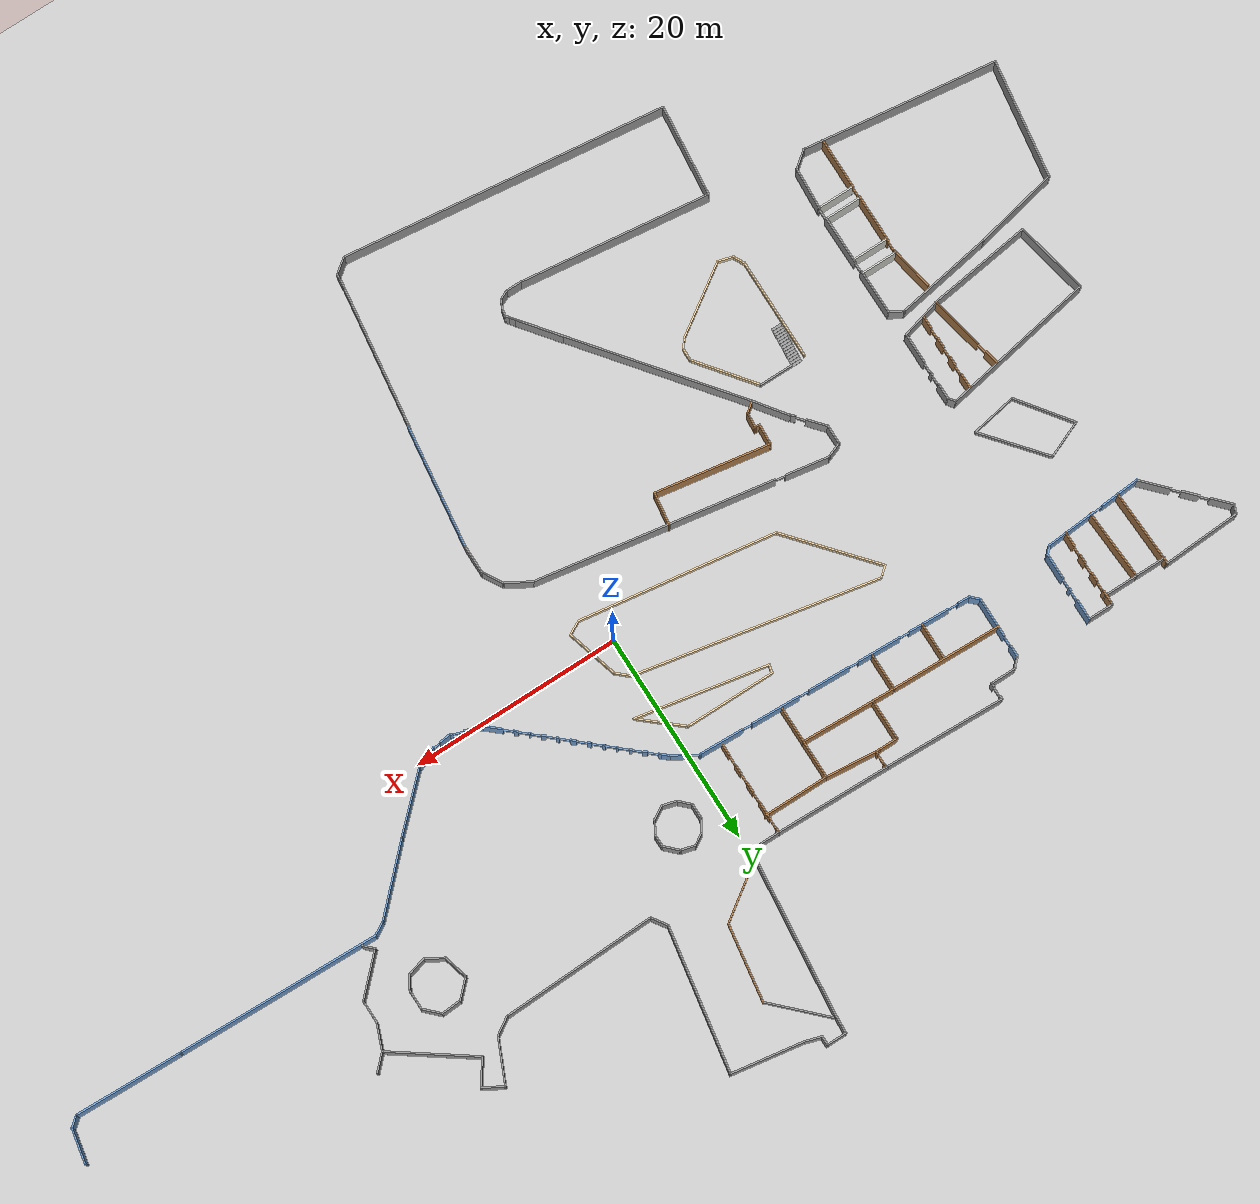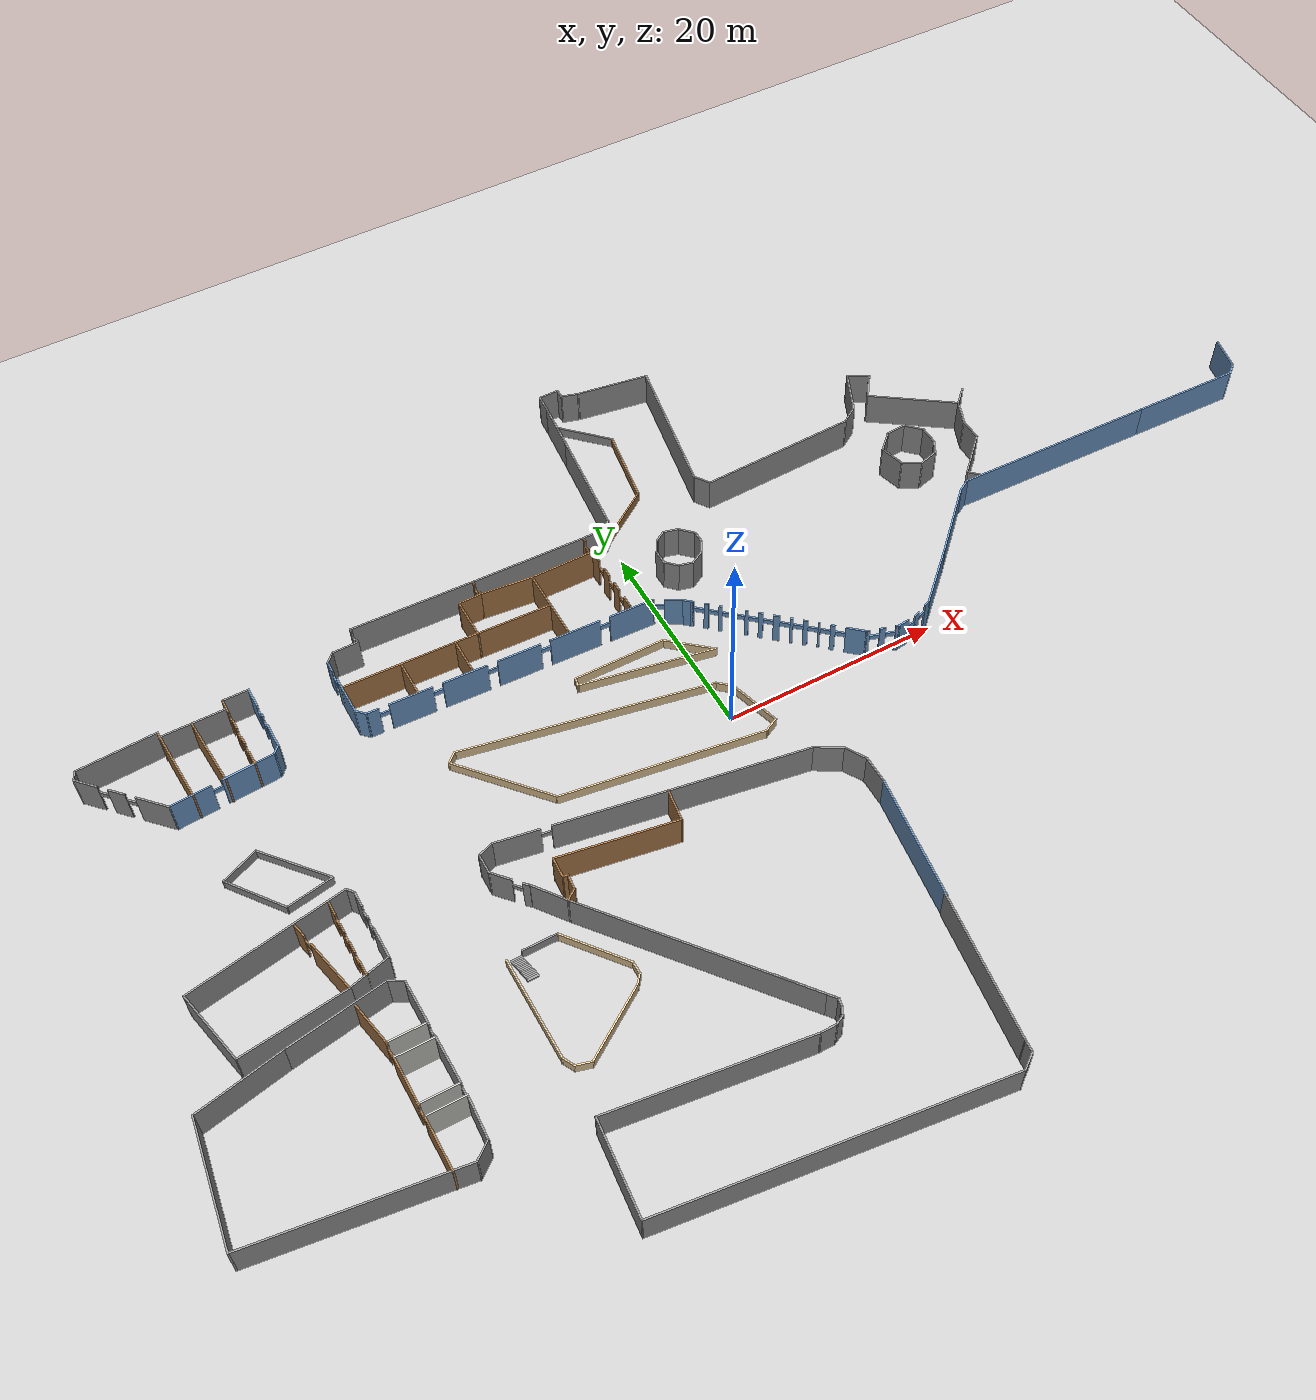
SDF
<sdf version="1.6">
 <world name="default">
  <light name="sun" type="directional">
   <pose>0 0 10 0 -0 0</pose>
   <diffuse>0.8 0.8 0.8 1</diffuse>
   <specular>0.2 0.2 0.2 1</specular>
   <attenuation>
    <range>1000</range>
    <constant>0.9</constant>
    <linear>0.01</linear>
    <quadratic>0.001</quadratic>
   </attenuation>
   <direction>-0.5 0.1 -0.9</direction>
  </light>
  <model name="ground_plane">
   <static>1</static>
   <link name="link">
    <collision name="collision">
     <geometry><plane><normal>0 0 1</normal><size>100 100</size></plane></geometry>
     <surface><friction><ode><mu>100</mu><mu2>50</mu2></ode></friction></surface>
    </collision>
    <visual name="visual">
     <cast_shadows>0</cast_shadows>
     <geometry><plane><normal>0 0 1</normal><size>100 100</size></plane></geometry>
     <material>
      <script><uri>file://media/materials/scripts/gazebo.material</uri><name>Gazebo/Grey</name></script>
     </material>
    </visual>
   </link>
  </model>
  <gravity>0 0 -9.8</gravity>
  <magnetic_field>6e-06 2.3e-05 -4.2e-05</magnetic_field>
  <atmosphere type="adiabatic"/>
  <physics name="default_physics" default="0" type="ode">
   <max_step_size>0.001</max_step_size>
   <real_time_factor>1</real_time_factor>
   <real_time_update_rate>1000</real_time_update_rate>
  </physics>
  <scene><ambient>0.4 0.4 0.4 1</ambient><background>0.7 0.7 0.7 1</background><shadows>1</shadows></scene>
  <audio><device>default</device></audio>
  <spherical_coordinates>
   <surface_model>EARTH_WGS84</surface_model>
   <latitude_deg>0</latitude_deg>
   <longitude_deg>0</longitude_deg>
   <elevation>0</elevation>
   <heading_deg>0</heading_deg>
  </spherical_coordinates>
  <model name="compound">
   <pose>3.54588 -0.628009 0 0 -0 0</pose>
   <link name="Stairs_2">
    <visual name="Stairs_2_Visual_0">
     <pose>-29.986 -11.3674 0.083333 0 -0 0</pose>
     <geometry><box><size>1 0.233333 0.166667</size></box></geometry>
     <material>
      <script><uri>file://media/materials/scripts/gazebo.material</uri><name>Gazebo/Grey</name></script>
      <ambient>1 1 1 1</ambient>
     </material>
     <meta><layer>0</layer></meta>
    </visual>
    <collision name="Stairs_2_Collision_0">
     <geometry><box><size>1 0.233333 0.166667</size></box></geometry>
     <pose>-29.986 -11.3674 0.083333 0 -0 0</pose>
    </collision>
    <visual name="Stairs_2_Visual_1">
     <pose>-29.986 -11.6007 0.25 0 -0 0</pose>
     <geometry><box><size>1 0.233333 0.166667</size></box></geometry>
     <material>
      <script><uri>file://media/materials/scripts/gazebo.material</uri><name>Gazebo/Grey</name></script>
      <ambient>1 1 1 1</ambient>
     </material>
     <meta><layer>0</layer></meta>
    </visual>
    <collision name="Stairs_2_Collision_1">
     <geometry><box><size>1 0.233333 0.166667</size></box></geometry>
     <pose>-29.986 -11.6007 0.25 0 -0 0</pose>
    </collision>
    <visual name="Stairs_2_Visual_2">
     <pose>-29.986 -11.8341 0.416667 0 -0 0</pose>
     <geometry><box><size>1 0.233333 0.166667</size></box></geometry>
     <material>
      <script><uri>file://media/materials/scripts/gazebo.material</uri><name>Gazebo/Grey</name></script>
      <ambient>1 1 1 1</ambient>
     </material>
     <meta><layer>0</layer></meta>
    </visual>
    <collision name="Stairs_2_Collision_2">
     <geometry><box><size>1 0.233333 0.166667</size></box></geometry>
     <pose>-29.986 -11.8341 0.416667 0 -0 0</pose>
    </collision>
    <visual name="Stairs_2_Visual_3">
     <pose>-29.986 -12.0674 0.583333 0 -0 0</pose>
     <geometry><box><size>1 0.233333 0.166667</size></box></geometry>
     <material>
      <script><uri>file://media/materials/scripts/gazebo.material</uri><name>Gazebo/Grey</name></script>
      <ambient>1 1 1 1</ambient>
     </material>
     <meta><layer>0</layer></meta>
    </visual>
    <collision name="Stairs_2_Collision_3">
     <geometry><box><size>1 0.233333 0.166667</size></box></geometry>
     <pose>-29.986 -12.0674 0.583333 0 -0 0</pose>
    </collision>
    <visual name="Stairs_2_Visual_4">
     <pose>-29.986 -12.3007 0.75 0 -0 0</pose>
     <geometry><box><size>1 0.233333 0.166667</size></box></geometry>
     <material>
      <script><uri>file://media/materials/scripts/gazebo.material</uri><name>Gazebo/Grey</name></script>
      <ambient>1 1 1 1</ambient>
     </material>
     <meta><layer>0</layer></meta>
    </visual>
    <collision name="Stairs_2_Collision_4">
     <geometry><box><size>1 0.233333 0.166667</size></box></geometry>
     <pose>-29.986 -12.3007 0.75 0 -0 0</pose>
    </collision>
    <visual name="Stairs_2_Visual_5">
     <pose>-29.986 -12.5341 0.916667 0 -0 0</pose>
     <geometry><box><size>1 0.233333 0.166667</size></box></geometry>
     <material>
      <script><uri>file://media/materials/scripts/gazebo.material</uri><name>Gazebo/Grey</name></script>
      <ambient>1 1 1 1</ambient>
     </material>
     <meta><layer>0</layer></meta>
    </visual>
    <collision name="Stairs_2_Collision_5">
     <geometry><box><size>1 0.233333 0.166667</size></box></geometry>
     <pose>-29.986 -12.5341 0.916667 0 -0 0</pose>
    </collision>
    <visual name="Stairs_2_Visual_6">
     <pose>-29.986 -12.7674 1.08333 0 -0 0</pose>
     <geometry><box><size>1 0.233333 0.166667</size></box></geometry>
     <material>
      <script><uri>file://media/materials/scripts/gazebo.material</uri><name>Gazebo/Grey</name></script>
      <ambient>1 1 1 1</ambient>
     </material>
     <meta><layer>0</layer></meta>
    </visual>
    <collision name="Stairs_2_Collision_6">
     <geometry><box><size>1 0.233333 0.166667</size></box></geometry>
     <pose>-29.986 -12.7674 1.08333 0 -0 0</pose>
    </collision>
    <visual name="Stairs_2_Visual_7">
     <pose>-29.986 -13.0007 1.25 0 -0 0</pose>
     <geometry><box><size>1 0.233333 0.166667</size></box></geometry>
     <material>
      <script><uri>file://media/materials/scripts/gazebo.material</uri><name>Gazebo/Grey</name></script>
      <ambient>1 1 1 1</ambient>
     </material>
     <meta><layer>0</layer></meta>
    </visual>
    <collision name="Stairs_2_Collision_7">
     <geometry><box><size>1 0.233333 0.166667</size></box></geometry>
     <pose>-29.986 -13.0007 1.25 0 -0 0</pose>
    </collision>
    <visual name="Stairs_2_Visual_8">
     <pose>-29.986 -13.2341 1.41667 0 -0 0</pose>
     <geometry><box><size>1 0.233333 0.166667</size></box></geometry>
     <material>
      <script><uri>file://media/materials/scripts/gazebo.material</uri><name>Gazebo/Grey</name></script>
      <ambient>1 1 1 1</ambient>
     </material>
     <meta><layer>0</layer></meta>
    </visual>
    <collision name="Stairs_2_Collision_8">
     <geometry><box><size>1 0.233333 0.166667</size></box></geometry>
     <pose>-29.986 -13.2341 1.41667 0 -0 0</pose>
    </collision>
    <visual name="Stairs_2_Visual_9">
     <pose>-29.986 -13.4674 1.58333 0 -0 0</pose>
     <geometry><box><size>1 0.233333 0.166667</size></box></geometry>
     <material>
      <script><uri>file://media/materials/scripts/gazebo.material</uri><name>Gazebo/Grey</name></script>
      <ambient>1 1 1 1</ambient>
     </material>
     <meta><layer>0</layer></meta>
    </visual>
    <collision name="Stairs_2_Collision_9">
     <geometry><box><size>1 0.233333 0.166667</size></box></geometry>
     <pose>-29.986 -13.4674 1.58333 0 -0 0</pose>
    </collision>
    <visual name="Stairs_2_Visual_10">
     <pose>-29.986 -13.7007 1.75 0 -0 0</pose>
     <geometry><box><size>1 0.233333 0.166667</size></box></geometry>
     <material>
      <script><uri>file://media/materials/scripts/gazebo.material</uri><name>Gazebo/Grey</name></script>
      <ambient>1 1 1 1</ambient>
     </material>
     <meta><layer>0</layer></meta>
    </visual>
    <collision name="Stairs_2_Collision_10">
     <geometry><box><size>1 0.233333 0.166667</size></box></geometry>
     <pose>-29.986 -13.7007 1.75 0 -0 0</pose>
    </collision>
    <visual name="Stairs_2_Visual_11">
     <pose>-29.986 -13.9341 1.91667 0 -0 0</pose>
     <geometry><box><size>1 0.233333 0.166667</size></box></geometry>
     <material>
      <script><uri>file://media/materials/scripts/gazebo.material</uri><name>Gazebo/Grey</name></script>
      <ambient>1 1 1 1</ambient>
     </material>
     <meta><layer>0</layer></meta>
    </visual>
    <collision name="Stairs_2_Collision_11">
     <geometry><box><size>1 0.233333 0.166667</size></box></geometry>
     <pose>-29.986 -13.9341 1.91667 0 -0 0</pose>
    </collision>
    <visual name="Stairs_2_Visual_12">
     <pose>-29.986 -14.1674 2.08333 0 -0 0</pose>
     <geometry><box><size>1 0.233333 0.166667</size></box></geometry>
     <material>
      <script><uri>file://media/materials/scripts/gazebo.material</uri><name>Gazebo/Grey</name></script>
      <ambient>1 1 1 1</ambient>
     </material>
     <meta><layer>0</layer></meta>
    </visual>
    <collision name="Stairs_2_Collision_12">
     <geometry><box><size>1 0.233333 0.166667</size></box></geometry>
     <pose>-29.986 -14.1674 2.08333 0 -0 0</pose>
    </collision>
    <visual name="Stairs_2_Visual_13">
     <pose>-29.986 -14.4007 2.25 0 -0 0</pose>
     <geometry><box><size>1 0.233333 0.166667</size></box></geometry>
     <material>
      <script><uri>file://media/materials/scripts/gazebo.material</uri><name>Gazebo/Grey</name></script>
      <ambient>1 1 1 1</ambient>
     </material>
     <meta><layer>0</layer></meta>
    </visual>
    <collision name="Stairs_2_Collision_13">
     <geometry><box><size>1 0.233333 0.166667</size></box></geometry>
     <pose>-29.986 -14.4007 2.25 0 -0 0</pose>
    </collision>
    <visual name="Stairs_2_Visual_14">
     <pose>-29.986 -14.6341 2.41667 0 -0 0</pose>
     <geometry><box><size>1 0.233333 0.166667</size></box></geometry>
     <material>
      <script><uri>file://media/materials/scripts/gazebo.material</uri><name>Gazebo/Grey</name></script>
      <ambient>1 1 1 1</ambient>
     </material>
     <meta><layer>0</layer></meta>
    </visual>
    <collision name="Stairs_2_Collision_14">
     <geometry><box><size>1 0.233333 0.166667</size></box></geometry>
     <pose>-29.986 -14.6341 2.41667 0 -0 0</pose>
    </collision>
   </link>
   <link name="Wall_1">
    <pose>-17.7632 13.6017 0 0 -0 3.10436</pose>
    <visual name="Wall_1_Visual_0">
     <pose>-11.3294 0 1.25 0 -0 0</pose>
     <geometry><box><size>4.30756 0.15 4.0</size></box></geometry>
     <material>
      <script><uri>file://media/materials/scripts/gazebo.material</uri><name>Gazebo/Grey</name></script>
      <ambient>0.447059 0.623529 0.811765 1</ambient>
     </material>
     <meta><layer>0</layer></meta>
    </visual>
    <collision name="Wall_1_Collision_0">
     <geometry><box><size>4.30756 0.15 4.0</size></box></geometry>
     <pose>-11.3294 0 1.25 0 -0 0</pose>
    </collision>
    <visual name="Wall_1_Visual_1">
     <pose>-5.89487 0 1.25 0 -0 0</pose>
     <geometry><box><size>4.76144 0.15 4.0</size></box></geometry>
     <material>
      <script><uri>file://media/materials/scripts/gazebo.material</uri><name>Gazebo/Grey</name></script>
      <ambient>0.447059 0.623529 0.811765 1</ambient>
     </material>
     <meta><layer>0</layer></meta>
    </visual>
    <collision name="Wall_1_Collision_1">
     <geometry><box><size>4.76144 0.15 4.0</size></box></geometry>
     <pose>-5.89487 0 1.25 0 -0 0</pose>
    </collision>
    <visual name="Wall_1_Visual_2">
     <pose>-0.581414 0 1.25 0 -0 0</pose>
     <geometry><box><size>4.06547 0.15 4.0</size></box></geometry>
     <material>
      <script><uri>file://media/materials/scripts/gazebo.material</uri><name>Gazebo/Grey</name></script>
      <ambient>0.447059 0.623529 0.811765 1</ambient>
     </material>
     <meta><layer>0</layer></meta>
    </visual>
    <collision name="Wall_1_Collision_2">
     <geometry><box><size>4.06547 0.15 4.0</size></box></geometry>
     <pose>-0.581414 0 1.25 0 -0 0</pose>
    </collision>
    <visual name="Wall_1_Visual_3">
     <pose>4.42952 0 1.25 0 -0 0</pose>
     <geometry><box><size>4.15639 0.15 4.0</size></box></geometry>
     <material>
      <script><uri>file://media/materials/scripts/gazebo.material</uri><name>Gazebo/Grey</name></script>
      <ambient>0.447059 0.623529 0.811765 1</ambient>
     </material>
     <meta><layer>0</layer></meta>
    </visual>
    <collision name="Wall_1_Collision_3">
     <geometry><box><size>4.15639 0.15 4.0</size></box></geometry>
     <pose>4.42952 0 1.25 0 -0 0</pose>
    </collision>
    <visual name="Wall_1_Visual_4">
     <pose>9.39757 0 1.25 0 -0 0</pose>
     <geometry><box><size>3.97971 0.15 4.0</size></box></geometry>
     <material>
      <script><uri>file://media/materials/scripts/gazebo.material</uri><name>Gazebo/Grey</name></script>
      <ambient>0.447059 0.623529 0.811765 1</ambient>
     </material>
     <meta><layer>0</layer></meta>
    </visual>
    <collision name="Wall_1_Collision_4">
     <geometry><box><size>3.97971 0.15 4.0</size></box></geometry>
     <pose>9.39757 0 1.25 0 -0 0</pose>
    </collision>
    <visual name="Wall_1_Visual_5">
     <pose>12.8853 0 1.25 0 -0 0</pose>
     <geometry><box><size>1.19573 0.15 4.0</size></box></geometry>
     <material>
      <script><uri>file://media/materials/scripts/gazebo.material</uri><name>Gazebo/Grey</name></script>
      <ambient>0.447059 0.623529 0.811765 1</ambient>
     </material>
     <meta><layer>0</layer></meta>
    </visual>
    <collision name="Wall_1_Collision_5">
     <geometry><box><size>1.19573 0.15 4.0</size></box></geometry>
     <pose>12.8853 0 1.25 0 -0 0</pose>
    </collision>
    <visual name="Wall_1_Visual_6">
     <pose>-8.72559 0 2.25 0 -0 0</pose>
     <geometry><box><size>0.9 0.15 0.5</size></box></geometry>
     <material>
      <script><uri>file://media/materials/scripts/gazebo.material</uri><name>Gazebo/Grey</name></script>
      <ambient>0.447059 0.623529 0.811765 1</ambient>
     </material>
     <meta><layer>0</layer></meta>
    </visual>
    <collision name="Wall_1_Collision_6">
     <geometry><box><size>0.9 0.15 0.5</size></box></geometry>
     <pose>-8.72559 0 2.25 0 -0 0</pose>
    </collision>
    <visual name="Wall_1_Visual_7">
     <pose>-3.06415 0 2.25 0 -0 0</pose>
     <geometry><box><size>0.9 0.15 0.5</size></box></geometry>
     <material>
      <script><uri>file://media/materials/scripts/gazebo.material</uri><name>Gazebo/Grey</name></script>
      <ambient>0.447059 0.623529 0.811765 1</ambient>
     </material>
     <meta><layer>0</layer></meta>
    </visual>
    <collision name="Wall_1_Collision_7">
     <geometry><box><size>0.9 0.15 0.5</size></box></geometry>
     <pose>-3.06415 0 2.25 0 -0 0</pose>
    </collision>
    <visual name="Wall_1_Visual_8">
     <pose>1.90132 0 2.25 0 -0 0</pose>
     <geometry><box><size>0.9 0.15 0.5</size></box></geometry>
     <material>
      <script><uri>file://media/materials/scripts/gazebo.material</uri><name>Gazebo/Grey</name></script>
      <ambient>0.447059 0.623529 0.811765 1</ambient>
     </material>
     <meta><layer>0</layer></meta>
    </visual>
    <collision name="Wall_1_Collision_8">
     <geometry><box><size>0.9 0.15 0.5</size></box></geometry>
     <pose>1.90132 0 2.25 0 -0 0</pose>
    </collision>
    <visual name="Wall_1_Visual_9">
     <pose>6.95771 0 2.25 0 -0 0</pose>
     <geometry><box><size>0.9 0.15 0.5</size></box></geometry>
     <material>
      <script><uri>file://media/materials/scripts/gazebo.material</uri><name>Gazebo/Grey</name></script>
      <ambient>0.447059 0.623529 0.811765 1</ambient>
     </material>
     <meta><layer>0</layer></meta>
    </visual>
    <collision name="Wall_1_Collision_9">
     <geometry><box><size>0.9 0.15 0.5</size></box></geometry>
     <pose>6.95771 0 2.25 0 -0 0</pose>
    </collision>
    <visual name="Wall_1_Visual_10">
     <pose>11.8374 0 2.25 0 -0 0</pose>
     <geometry><box><size>0.9 0.15 0.5</size></box></geometry>
     <material>
      <script><uri>file://media/materials/scripts/gazebo.material</uri><name>Gazebo/Grey</name></script>
      <ambient>0.447059 0.623529 0.811765 1</ambient>
     </material>
     <meta><layer>0</layer></meta>
    </visual>
    <collision name="Wall_1_Collision_10">
     <geometry><box><size>0.9 0.15 0.5</size></box></geometry>
     <pose>11.8374 0 2.25 0 -0 0</pose>
    </collision>
   </link>
   <link name="Wall_100">
    <collision name="Wall_100_Collision">
     <geometry><box><size>1.2615 0.15 4.0</size></box></geometry>
     <pose>0 0 1.25 0 -0 0</pose>
    </collision>
    <visual name="Wall_100_Visual">
     <pose>0 0 1.25 0 -0 0</pose>
     <geometry><box><size>1.2615 0.15 4.0</size></box></geometry>
     <material>
      <script><uri>file://media/materials/scripts/gazebo.material</uri><name>Gazebo/Wood</name></script>
      <ambient>1 1 1 1</ambient>
     </material>
     <meta><layer>0</layer></meta>
    </visual>
    <pose>-24.2062 -9.9319 0 0 -0 -2.50221</pose>
   </link>
   <link name="Wall_101">
    <collision name="Wall_101_Collision">
     <geometry><box><size>3.61722 0.15 4.0</size></box></geometry>
     <pose>0 0 1.25 0 -0 0</pose>
    </collision>
    <visual name="Wall_101_Visual">
     <pose>0 0 1.25 0 -0 0</pose>
     <geometry><box><size>3.61722 0.15 4.0</size></box></geometry>
     <material>
      <script><uri>file://media/materials/scripts/gazebo.material</uri><name>Gazebo/Grey</name></script>
      <ambient>1 1 1 1</ambient>
     </material>
     <meta><layer>0</layer></meta>
    </visual>
    <pose>-25.6814 -8.86844 0 0 -0 2.20638</pose>
   </link>
   <link name="Wall_103">
    <collision name="Wall_103_Collision">
     <geometry><box><size>22.2877 0.15 4.0</size></box></geometry>
     <pose>0 0 1.25 0 -0 0</pose>
    </collision>
    <visual name="Wall_103_Visual">
     <pose>0 0 1.25 0 -0 0</pose>
     <geometry><box><size>22.2877 0.15 4.0</size></box></geometry>
     <material>
      <script><uri>file://media/materials/scripts/gazebo.material</uri><name>Gazebo/Grey</name></script>
      <ambient>1 1 1 1</ambient>
     </material>
     <meta><layer>0</layer></meta>
    </visual>
    <pose>-17.8037 -18.9593 0 0 -0 -0.903682</pose>
   </link>
   <link name="Wall_105">
    <collision name="Wall_105_Collision">
     <geometry><box><size>5.39481 0.15 4.0</size></box></geometry>
     <pose>0 0 1.25 0 -0 0</pose>
    </collision>
    <visual name="Wall_105_Visual">
     <pose>0 0 1.25 0 -0 0</pose>
     <geometry><box><size>5.39481 0.15 4.0</size></box></geometry>
     <material>
      <script><uri>file://media/materials/scripts/gazebo.material</uri><name>Gazebo/Grey</name></script>
      <ambient>1 1 1 1</ambient>
     </material>
     <meta><layer>0</layer></meta>
    </visual>
    <pose>-12.2975 -25.9342 0 0 -0 -0.909753</pose>
   </link>
   <link name="Wall_106">
    <collision name="Wall_106_Collision">
     <geometry><box><size>0.853665 0.15 4.0</size></box></geometry>
     <pose>0 0 1.25 0 -0 0</pose>
    </collision>
    <visual name="Wall_106_Visual">
     <pose>0 0 1.25 0 -0 0</pose>
     <geometry><box><size>0.853665 0.15 4.0</size></box></geometry>
     <material>
      <script><uri>file://media/materials/scripts/gazebo.material</uri><name>Gazebo/Grey</name></script>
      <ambient>1 1 1 1</ambient>
     </material>
     <meta><layer>0</layer></meta>
    </visual>
    <pose>-10.7565 -28.3492 0 0 -0 -1.76819</pose>
   </link>
   <link name="Wall_107">
    <collision name="Wall_107_Collision">
     <geometry><box><size>0.972873 0.15 4.0</size></box></geometry>
     <pose>0 0 1.25 0 -0 0</pose>
    </collision>
    <visual name="Wall_107_Visual">
     <pose>0 0 1.25 0 -0 0</pose>
     <geometry><box><size>0.972873 0.15 4.0</size></box></geometry>
     <material>
      <script><uri>file://media/materials/scripts/gazebo.material</uri><name>Gazebo/Grey</name></script>
      <ambient>1 1 1 1</ambient>
     </material>
     <meta><layer>0</layer></meta>
    </visual>
    <pose>-11.0095 -29.0623 0 0 -0 -2.03444</pose>
   </link>
   <link name="Wall_108">
    <collision name="Wall_108_Collision">
     <geometry><box><size>1.01426 0.15 4.0</size></box></geometry>
     <pose>0 0 1.25 0 -0 0</pose>
    </collision>
    <visual name="Wall_108_Visual">
     <pose>0 0 1.25 0 -0 0</pose>
     <geometry><box><size>1.01426 0.15 4.0</size></box></geometry>
     <material>
      <script><uri>file://media/materials/scripts/gazebo.material</uri><name>Gazebo/Grey</name></script>
      <ambient>1 1 1 1</ambient>
     </material>
     <meta><layer>0</layer></meta>
    </visual>
    <pose>-11.5845 -29.6142 0 0 -0 -2.70175</pose>
   </link>
   <link name="Wall_109">
    <collision name="Wall_109_Collision">
     <geometry><box><size>1.576 0.15 4.0</size></box></geometry>
     <pose>0 0 1.25 0 -0 0</pose>
    </collision>
    <visual name="Wall_109_Visual">
     <pose>0 0 1.25 0 -0 0</pose>
     <geometry><box><size>1.576 0.15 4.0</size></box></geometry>
     <material>
      <script><uri>file://media/materials/scripts/gazebo.material</uri><name>Gazebo/Grey</name></script>
      <ambient>1 1 1 1</ambient>
     </material>
     <meta><layer>0</layer></meta>
    </visual>
    <pose>-12.6885 -29.7983 0 0 -0 3.14159</pose>
   </link>
   <link name="Wall_110">
    <collision name="Wall_110_Collision">
     <geometry><box><size>18.1398 0.15 4.0</size></box></geometry>
     <pose>0 0 1.25 0 -0 0</pose>
    </collision>
    <visual name="Wall_110_Visual">
     <pose>0 0 1.25 0 -0 0</pose>
     <geometry><box><size>18.1398 0.15 4.0</size></box></geometry>
     <material>
      <script><uri>file://media/materials/scripts/gazebo.material</uri><name>Gazebo/Grey</name></script>
      <ambient>1 1 1 1</ambient>
     </material>
     <meta><layer>0</layer></meta>
    </visual>
    <pose>-22.3255 -28.6713 0 0 -0 3.01597</pose>
   </link>
   <link name="Wall_111">
    <collision name="Wall_111_Collision">
     <geometry><box><size>8.79176 0.15 4.0</size></box></geometry>
     <pose>0 0 1.25 0 -0 0</pose>
    </collision>
    <visual name="Wall_111_Visual">
     <pose>0 0 1.25 0 -0 0</pose>
     <geometry><box><size>8.79176 0.15 4.0</size></box></geometry>
     <material>
      <script><uri>file://media/materials/scripts/gazebo.material</uri><name>Gazebo/Grey</name></script>
      <ambient>1 1 1 1</ambient>
     </material>
     <meta><layer>0</layer></meta>
    </visual>
    <pose>-31.6635 -31.8453 0 0 -0 -1.66676</pose>
   </link>
   <link name="Wall_112">
    <collision name="Wall_112_Collision">
     <geometry><box><size>30.7378 0.15 4.0</size></box></geometry>
     <pose>0 0 1.25 0 -0 0</pose>
    </collision>
    <visual name="Wall_112_Visual">
     <pose>0 0 1.25 0 -0 0</pose>
     <geometry><box><size>30.7378 0.15 4.0</size></box></geometry>
     <material>
      <script><uri>file://media/materials/scripts/gazebo.material</uri><name>Gazebo/Grey</name></script>
      <ambient>1 1 1 1</ambient>
     </material>
     <meta><layer>0</layer></meta>
    </visual>
    <pose>-16.8975 -38.0092 0 0 -0 -0.122117</pose>
   </link>
   <link name="Wall_113">
    <collision name="Wall_113_Collision">
     <geometry><box><size>1.76 0.15 4.0</size></box></geometry>
     <pose>0 0 1.25 0 -0 0</pose>
    </collision>
    <visual name="Wall_113_Visual">
     <pose>0 0 1.25 0 -0 0</pose>
     <geometry><box><size>1.76 0.15 4.0</size></box></geometry>
     <material>
      <script><uri>file://media/materials/scripts/gazebo.material</uri><name>Gazebo/Grey</name></script>
      <ambient>1 1 1 1</ambient>
     </material>
     <meta><layer>0</layer></meta>
    </visual>
    <pose>-1.07346 -39.3892 0 0 -0 0.643501</pose>
   </link>
   <link name="Wall_114">
    <collision name="Wall_114_Collision">
     <geometry><box><size>1.16617 0.15 4.0</size></box></geometry>
     <pose>0 0 1.25 0 -0 0</pose>
    </collision>
    <visual name="Wall_114_Visual">
     <pose>0 0 1.25 0 -0 0</pose>
     <geometry><box><size>1.16617 0.15 4.0</size></box></geometry>
     <material>
      <script><uri>file://media/materials/scripts/gazebo.material</uri><name>Gazebo/Grey</name></script>
      <ambient>1 1 1 1</ambient>
     </material>
     <meta><layer>0</layer></meta>
    </visual>
    <pose>-0.383461 -38.4003 0 0 -0 1.48014</pose>
   </link>
   <link name="Wall_115">
    <collision name="Wall_115_Collision">
     <geometry><box><size>13.8837 0.15 4.0</size></box></geometry>
     <pose>0 0 1.25 0 -0 0</pose>
    </collision>
    <visual name="Wall_115_Visual">
     <pose>0 0 1.25 0 -0 0</pose>
     <geometry><box><size>13.8837 0.15 4.0</size></box></geometry>
     <material>
      <script><uri>file://media/materials/scripts/gazebo.material</uri><name>Gazebo/Grey</name></script>
      <ambient>1 1 1 1</ambient>
     </material>
     <meta><layer>0</layer></meta>
    </visual>
    <pose>0.559538 -31.0862 0 0 -0 1.43979</pose>
   </link>
   <link name="Wall_117">
    <collision name="Wall_117_Collision">
     <geometry><box><size>3.25 0.15 1</size></box></geometry>
     <pose>0 0 0.5 0 -0 0</pose>
    </collision>
    <visual name="Wall_117_Visual">
     <pose>0 0 0.5 0 -0 0</pose>
     <geometry><box><size>3.25 0.15 1</size></box></geometry>
     <material>
      <script><uri>file://media/materials/scripts/gazebo.material</uri><name>Gazebo/Grey</name></script>
      <ambient>1 1 1 1</ambient>
     </material>
     <meta><layer>0</layer></meta>
    </visual>
    <pose>-27.8447 -11.3314 0 0 -0 0</pose>
   </link>
   <link name="Wall_118">
    <collision name="Wall_118_Collision">
     <geometry><box><size>6.66654 0.15 1</size></box></geometry>
     <pose>0 0 0.5 0 -0 0</pose>
    </collision>
    <visual name="Wall_118_Visual">
     <pose>0 0 0.5 0 -0 0</pose>
     <geometry><box><size>6.66654 0.15 1</size></box></geometry>
     <material>
      <script><uri>file://media/materials/scripts/gazebo.material</uri><name>Gazebo/Grey</name></script>
      <ambient>0.921569 0.807843 0.615686 1</ambient>
     </material>
     <meta><layer>0</layer></meta>
    </visual>
    <pose>-24.2967 -13.9054 0 0 -0 -0.910722</pose>
   </link>
   <link name="Wall_119">
    <collision name="Wall_119_Collision">
     <geometry><box><size>1.29783 0.15 1</size></box></geometry>
     <pose>0 0 0.5 0 -0 0</pose>
    </collision>
    <visual name="Wall_119_Visual">
     <pose>0 0 0.5 0 -0 0</pose>
     <geometry><box><size>1.29783 0.15 1</size></box></geometry>
     <material>
      <script><uri>file://media/materials/scripts/gazebo.material</uri><name>Gazebo/Grey</name></script>
      <ambient>0.921569 0.807843 0.615686 1</ambient>
     </material>
     <meta><layer>0</layer></meta>
    </visual>
    <pose>-22.2987 -17.0529 0 0 -0 -1.5708</pose>
   </link>
   <link name="Wall_120">
    <collision name="Wall_120_Collision">
     <geometry><box><size>1.13871 0.15 1</size></box></geometry>
     <pose>0 0 0.5 0 -0 0</pose>
    </collision>
    <visual name="Wall_120_Visual">
     <pose>0 0 0.5 0 -0 0</pose>
     <geometry><box><size>1.13871 0.15 1</size></box></geometry>
     <material>
      <script><uri>file://media/materials/scripts/gazebo.material</uri><name>Gazebo/Grey</name></script>
      <ambient>0.921569 0.807843 0.615686 1</ambient>
     </material>
     <meta><layer>0</layer></meta>
    </visual>
    <pose>-22.6117 -18.0094 0 0 -0 -2.25596</pose>
   </link>
   <link name="Wall_121">
    <collision name="Wall_121_Collision">
     <geometry><box><size>7.46263 0.15 1</size></box></geometry>
     <pose>0 0 0.5 0 -0 0</pose>
    </collision>
    <visual name="Wall_121_Visual">
     <pose>0 0 0.5 0 -0 0</pose>
     <geometry><box><size>7.46263 0.15 1</size></box></geometry>
     <material>
      <script><uri>file://media/materials/scripts/gazebo.material</uri><name>Gazebo/Grey</name></script>
      <ambient>0.921569 0.807843 0.615686 1</ambient>
     </material>
     <meta><layer>0</layer></meta>
    </visual>
    <pose>-25.9512 -20.4444 0 0 -0 -2.54578</pose>
   </link>
   <link name="Wall_122">
    <collision name="Wall_122_Collision">
     <geometry><box><size>1.55945 0.15 1</size></box></geometry>
     <pose>0 0 0.5 0 -0 0</pose>
    </collision>
    <visual name="Wall_122_Visual">
     <pose>0 0 0.5 0 -0 0</pose>
     <geometry><box><size>1.55945 0.15 1</size></box></geometry>
     <material>
      <script><uri>file://media/materials/scripts/gazebo.material</uri><name>Gazebo/Grey</name></script>
      <ambient>0.921569 0.807843 0.615686 1</ambient>
     </material>
     <meta><layer>0</layer></meta>
    </visual>
    <pose>-29.6557 -22.3049 0 0 -0 2.86632</pose>
   </link>
   <link name="Wall_123">
    <collision name="Wall_123_Collision">
     <geometry><box><size>1.28564 0.15 1</size></box></geometry>
     <pose>0 0 0.5 0 -0 0</pose>
    </collision>
    <visual name="Wall_123_Visual">
     <pose>0 0 0.5 0 -0 0</pose>
     <geometry><box><size>1.28564 0.15 1</size></box></geometry>
     <material>
      <script><uri>file://media/materials/scripts/gazebo.material</uri><name>Gazebo/Grey</name></script>
      <ambient>0.921569 0.807843 0.615686 1</ambient>
     </material>
     <meta><layer>0</layer></meta>
    </visual>
    <pose>-30.5947 -21.6094 0 0 -0 2.04863</pose>
   </link>
   <link name="Wall_126">
    <collision name="Wall_126_Collision">
     <geometry><box><size>9.35636 0.15 4.0</size></box></geometry>
     <pose>0 0 1.25 0 -0 0</pose>
    </collision>
    <visual name="Wall_126_Visual">
     <pose>0 0 1.25 0 -0 0</pose>
     <geometry><box><size>9.35636 0.15 4.0</size></box></geometry>
     <material>
      <script><uri>file://media/materials/scripts/gazebo.material</uri><name>Gazebo/Grey</name></script>
      <ambient>1 1 1 1</ambient>
     </material>
     <meta><layer>0</layer></meta>
    </visual>
    <pose>-44.5077 -10.5659 0 0 -0 0.167012</pose>
   </link>
   <link name="Wall_127">
    <collision name="Wall_127_Collision">
     <geometry><box><size>1.52204 0.15 4.0</size></box></geometry>
     <pose>0 0 1.25 0 -0 0</pose>
    </collision>
    <visual name="Wall_127_Visual">
     <pose>0 0 1.25 0 -0 0</pose>
     <geometry><box><size>1.52204 0.15 4.0</size></box></geometry>
     <material>
      <script><uri>file://media/materials/scripts/gazebo.material</uri><name>Gazebo/Grey</name></script>
      <ambient>1 1 1 1</ambient>
     </material>
     <meta><layer>0</layer></meta>
    </visual>
    <pose>-39.3773 -10.1486 0 0 -0 -0.531724</pose>
   </link>
   <link name="Wall_128">
    <pose>-38.7338 -15.9399 0 0 -0 -1.56121</pose>
    <visual name="Wall_128_Visual_0">
     <pose>-3.32744 0 1.25 0 -0 0</pose>
     <geometry><box><size>4.38207 0.15 4.0</size></box></geometry>
     <material>
      <script><uri>file://media/materials/scripts/gazebo.material</uri><name>Gazebo/Grey</name></script>
      <ambient>1 1 1 1</ambient>
     </material>
     <meta><layer>0</layer></meta>
    </visual>
    <collision name="Wall_128_Collision_0">
     <geometry><box><size>4.38207 0.15 4.0</size></box></geometry>
     <pose>-3.32744 0 1.25 0 -0 0</pose>
    </collision>
    <visual name="Wall_128_Visual_1">
     <pose>2.09262 0 1.25 0 -0 0</pose>
     <geometry><box><size>4.65806 0.15 4.0</size></box></geometry>
     <material>
      <script><uri>file://media/materials/scripts/gazebo.material</uri><name>Gazebo/Grey</name></script>
      <ambient>1 1 1 1</ambient>
     </material>
     <meta><layer>0</layer></meta>
    </visual>
    <collision name="Wall_128_Collision_1">
     <geometry><box><size>4.65806 0.15 4.0</size></box></geometry>
     <pose>2.09262 0 1.25 0 -0 0</pose>
    </collision>
    <visual name="Wall_128_Visual_2">
     <pose>5.42007 0 1.25 0 -0 0</pose>
     <geometry><box><size>0.196825 0.15 4.0</size></box></geometry>
     <material>
      <script><uri>file://media/materials/scripts/gazebo.material</uri><name>Gazebo/Grey</name></script>
      <ambient>1 1 1 1</ambient>
     </material>
     <meta><layer>0</layer></meta>
    </visual>
    <collision name="Wall_128_Collision_2">
     <geometry><box><size>0.196825 0.15 4.0</size></box></geometry>
     <pose>5.42007 0 1.25 0 -0 0</pose>
    </collision>
    <visual name="Wall_128_Visual_3">
     <pose>-0.68641 0 2.25 0 -0 0</pose>
     <geometry><box><size>0.9 0.15 0.5</size></box></geometry>
     <material>
      <script><uri>file://media/materials/scripts/gazebo.material</uri><name>Gazebo/Grey</name></script>
      <ambient>1 1 1 1</ambient>
     </material>
     <meta><layer>0</layer></meta>
    </visual>
    <collision name="Wall_128_Collision_3">
     <geometry><box><size>0.9 0.15 0.5</size></box></geometry>
     <pose>-0.68641 0 2.25 0 -0 0</pose>
    </collision>
    <visual name="Wall_128_Visual_4">
     <pose>4.87165 0 2.25 0 -0 0</pose>
     <geometry><box><size>0.9 0.15 0.5</size></box></geometry>
     <material>
      <script><uri>file://media/materials/scripts/gazebo.material</uri><name>Gazebo/Grey</name></script>
      <ambient>1 1 1 1</ambient>
     </material>
     <meta><layer>0</layer></meta>
    </visual>
    <collision name="Wall_128_Collision_4">
     <geometry><box><size>0.9 0.15 0.5</size></box></geometry>
     <pose>4.87165 0 2.25 0 -0 0</pose>
    </collision>
   </link>
   <link name="Wall_13">
    <collision name="Wall_13_Collision">
     <geometry><box><size>9.90428 0.15 1</size></box></geometry>
     <pose>0 0 0.5 0 -0 0</pose>
    </collision>
    <visual name="Wall_13_Visual">
     <pose>0 0 0.5 0 -0 0</pose>
     <geometry><box><size>9.90428 0.15 1</size></box></geometry>
     <material>
      <script><uri>file://media/materials/scripts/gazebo.material</uri><name>Gazebo/Grey</name></script>
      <ambient>0.921569 0.807843 0.615686 1</ambient>
     </material>
     <meta><layer>0</layer></meta>
    </visual>
    <pose>-23.6257 3.99058 0 0 -0 2.27942</pose>
   </link>
   <link name="Wall_130">
    <collision name="Wall_130_Collision">
     <geometry><box><size>4.0821 0.15 4.0</size></box></geometry>
     <pose>0 0 1.25 0 -0 0</pose>
    </collision>
    <visual name="Wall_130_Visual">
     <pose>0 0 1.25 0 -0 0</pose>
     <geometry><box><size>4.0821 0.15 4.0</size></box></geometry>
     <material>
      <script><uri>file://media/materials/scripts/gazebo.material</uri><name>Gazebo/Grey</name></script>
      <ambient>1 1 1 1</ambient>
     </material>
     <meta><layer>0</layer></meta>
    </visual>
    <pose>-38.7887 -23.3465 0 0 -0 -1.62528</pose>
   </link>
   <link name="Wall_131">
    <collision name="Wall_131_Collision">
     <geometry><box><size>1.97428 0.15 4.0</size></box></geometry>
     <pose>0 0 1.25 0 -0 0</pose>
    </collision>
    <visual name="Wall_131_Visual">
     <pose>0 0 1.25 0 -0 0</pose>
     <geometry><box><size>1.97428 0.15 4.0</size></box></geometry>
     <material>
      <script><uri>file://media/materials/scripts/gazebo.material</uri><name>Gazebo/Grey</name></script>
      <ambient>1 1 1 1</ambient>
     </material>
     <meta><layer>0</layer></meta>
    </visual>
    <pose>-39.6158 -25.8696 0 0 -0 -2.48055</pose>
   </link>
   <link name="Wall_132">
    <collision name="Wall_132_Collision">
     <geometry><box><size>18.4679 0.15 4.0</size></box></geometry>
     <pose>0 0 1.25 0 -0 0</pose>
    </collision>
    <visual name="Wall_132_Visual">
     <pose>0 0 1.25 0 -0 0</pose>
     <geometry><box><size>18.4679 0.15 4.0</size></box></geometry>
     <material>
      <script><uri>file://media/materials/scripts/gazebo.material</uri><name>Gazebo/Grey</name></script>
      <ambient>1 1 1 1</ambient>
     </material>
     <meta><layer>0</layer></meta>
    </visual>
    <pose>-49.4158 -25.2296 0 0 -0 3.0102</pose>
   </link>
   <link name="Wall_134">
    <collision name="Wall_134_Collision">
     <geometry><box><size>8.21137 0.15 4.0</size></box></geometry>
     <pose>0 0 1.25 0 -0 0</pose>
    </collision>
    <visual name="Wall_134_Visual">
     <pose>0 0 1.25 0 -0 0</pose>
     <geometry><box><size>8.21137 0.15 4.0</size></box></geometry>
     <material>
      <script><uri>file://media/materials/scripts/gazebo.material</uri><name>Gazebo/Grey</name></script>
      <ambient>1 1 1 1</ambient>
     </material>
     <meta><layer>0</layer></meta>
    </visual>
    <pose>-52.9913 -12.1604 0 0 -0 -2.93439</pose>
   </link>
   <link name="Wall_135">
    <collision name="Wall_135_Collision">
     <geometry><box><size>11.3053 0.15 4.0</size></box></geometry>
     <pose>0 0 1.25 0 -0 0</pose>
    </collision>
    <visual name="Wall_135_Visual">
     <pose>0 0 1.25 0 -0 0</pose>
     <geometry><box><size>11.3053 0.15 4.0</size></box></geometry>
     <material>
      <script><uri>file://media/materials/scripts/gazebo.material</uri><name>Gazebo/Grey</name></script>
      <ambient>1 1 1 1</ambient>
     </material>
     <meta><layer>0</layer></meta>
    </visual>
    <pose>-57.7358 -18.5096 0 0 -0 -1.71472</pose>
   </link>
   <link name="Wall_137">
    <collision name="Wall_137_Collision">
     <geometry><box><size>7.19936 0.15 4.0</size></box></geometry>
     <pose>0 0 1.25 0 -0 0</pose>
    </collision>
    <visual name="Wall_137_Visual">
     <pose>0 0 1.25 0 -0 0</pose>
     <geometry><box><size>7.19936 0.15 4.0</size></box></geometry>
     <material>
      <script><uri>file://media/materials/scripts/gazebo.material</uri><name>Gazebo/Grey</name></script>
      <ambient>1 1 1 1</ambient>
     </material>
     <meta><layer>0</layer></meta>
    </visual>
    <pose>-53.2303 -6.88402 0 0 -0 -1.35499</pose>
   </link>
   <link name="Wall_138">
    <collision name="Wall_138_Collision">
     <geometry><box><size>10.0396 0.15 4.0</size></box></geometry>
     <pose>0 0 1.25 0 -0 0</pose>
    </collision>
    <visual name="Wall_138_Visual">
     <pose>0 0 1.25 0 -0 0</pose>
     <geometry><box><size>10.0396 0.15 4.0</size></box></geometry>
     <material>
      <script><uri>file://media/materials/scripts/gazebo.material</uri><name>Gazebo/Grey</name></script>
      <ambient>1 1 1 1</ambient>
     </material>
     <meta><layer>0</layer></meta>
    </visual>
    <pose>-47.5758 -9.66154 0 0 -0 0.134977</pose>
   </link>
   <link name="Wall_14">
    <collision name="Wall_14_Collision">
     <geometry><box><size>1.29262 0.15 1</size></box></geometry>
     <pose>0 0 0.5 0 -0 0</pose>
    </collision>
    <visual name="Wall_14_Visual">
     <pose>0 0 0.5 0 -0 0</pose>
     <geometry><box><size>1.29262 0.15 1</size></box></geometry>
     <material>
      <script><uri>file://media/materials/scripts/gazebo.material</uri><name>Gazebo/Grey</name></script>
      <ambient>0.921569 0.807843 0.615686 1</ambient>
     </material>
     <meta><layer>0</layer></meta>
    </visual>
    <pose>-26.3627 8.06158 0 0 -0 0.699893</pose>
   </link>
   <link name="Wall_140">
    <collision name="Wall_140_Collision">
     <geometry><box><size>3.5 0.15 4.0</size></box></geometry>
     <pose>0 0 1.25 0 -0 0</pose>
    </collision>
    <visual name="Wall_140_Visual">
     <pose>0 0 1.25 0 -0 0</pose>
     <geometry><box><size>3.5 0.15 4.0</size></box></geometry>
     <material>
      <script><uri>file://media/materials/scripts/gazebo.material</uri><name>Gazebo/CeilingTiled</name></script>
      <ambient>1 1 1 1</ambient>
     </material>
     <meta><layer>0</layer></meta>
    </visual>
    <pose>-40.4795 -14.5311 0 0 -0 3.14159</pose>
   </link>
   <link name="Wall_142">
    <collision name="Wall_142_Collision">
     <geometry><box><size>4.16404 0.15 4.0</size></box></geometry>
     <pose>0 0 1.25 0 -0 0</pose>
    </collision>
    <visual name="Wall_142_Visual">
     <pose>0 0 1.25 0 -0 0</pose>
     <geometry><box><size>4.16404 0.15 4.0</size></box></geometry>
     <material>
      <script><uri>file://media/materials/scripts/gazebo.material</uri><name>Gazebo/Wood</name></script>
      <ambient>1 1 1 1</ambient>
     </material>
     <meta><layer>0</layer></meta>
    </visual>
    <pose>-42.5314 -12.5598 0 0 -0 -1.3819</pose>
   </link>
   <link name="Wall_143">
    <pose>-42.1545 -17.9561 0 0 -0 -1.5708</pose>
    <visual name="Wall_143_Visual_0">
     <pose>-3.3375 0 1.25 0 -0 0</pose>
     <geometry><box><size>0.324998 0.15 4.0</size></box></geometry>
     <material>
      <script><uri>file://media/materials/scripts/gazebo.material</uri><name>Gazebo/Wood</name></script>
      <ambient>1 1 1 1</ambient>
     </material>
     <meta><layer>0</layer></meta>
    </visual>
    <collision name="Wall_143_Collision_0">
     <geometry><box><size>0.324998 0.15 4.0</size></box></geometry>
     <pose>-3.3375 0 1.25 0 -0 0</pose>
    </collision>
    <visual name="Wall_143_Visual_1">
     <pose>0.110893 0 1.25 0 -0 0</pose>
     <geometry><box><size>4.77179 0.15 4.0</size></box></geometry>
     <material>
      <script><uri>file://media/materials/scripts/gazebo.material</uri><name>Gazebo/Wood</name></script>
      <ambient>1 1 1 1</ambient>
     </material>
     <meta><layer>0</layer></meta>
    </visual>
    <collision name="Wall_143_Collision_1">
     <geometry><box><size>4.77179 0.15 4.0</size></box></geometry>
     <pose>0.110893 0 1.25 0 -0 0</pose>
    </collision>
    <visual name="Wall_143_Visual_2">
     <pose>3.44839 0 1.25 0 -0 0</pose>
     <geometry><box><size>0.103211 0.15 4.0</size></box></geometry>
     <material>
      <script><uri>file://media/materials/scripts/gazebo.material</uri><name>Gazebo/Wood</name></script>
      <ambient>1 1 1 1</ambient>
     </material>
     <meta><layer>0</layer></meta>
    </visual>
    <collision name="Wall_143_Collision_2">
     <geometry><box><size>0.103211 0.15 4.0</size></box></geometry>
     <pose>3.44839 0 1.25 0 -0 0</pose>
    </collision>
    <visual name="Wall_143_Visual_3">
     <pose>-2.725 0 2.25 0 -0 0</pose>
     <geometry><box><size>0.9 0.15 0.5</size></box></geometry>
     <material>
      <script><uri>file://media/materials/scripts/gazebo.material</uri><name>Gazebo/Wood</name></script>
      <ambient>1 1 1 1</ambient>
     </material>
     <meta><layer>0</layer></meta>
    </visual>
    <collision name="Wall_143_Collision_3">
     <geometry><box><size>0.9 0.15 0.5</size></box></geometry>
     <pose>-2.725 0 2.25 0 -0 0</pose>
    </collision>
    <visual name="Wall_143_Visual_4">
     <pose>2.94679 0 2.25 0 -0 0</pose>
     <geometry><box><size>0.9 0.15 0.5</size></box></geometry>
     <material>
      <script><uri>file://media/materials/scripts/gazebo.material</uri><name>Gazebo/Wood</name></script>
      <ambient>1 1 1 1</ambient>
     </material>
     <meta><layer>0</layer></meta>
    </visual>
    <collision name="Wall_143_Collision_4">
     <geometry><box><size>0.9 0.15 0.5</size></box></geometry>
     <pose>2.94679 0 2.25 0 -0 0</pose>
    </collision>
   </link>
   <link name="Wall_144">
    <collision name="Wall_144_Collision">
     <geometry><box><size>3.62289 0.15 4.0</size></box></geometry>
     <pose>0 0 1.25 0 -0 0</pose>
    </collision>
    <visual name="Wall_144_Visual">
     <pose>0 0 1.25 0 -0 0</pose>
     <geometry><box><size>3.62289 0.15 4.0</size></box></geometry>
     <material>
      <script><uri>file://media/materials/scripts/gazebo.material</uri><name>Gazebo/CeilingTiled</name></script>
      <ambient>1 1 1 1</ambient>
     </material>
     <meta><layer>0</layer></meta>
    </visual>
    <pose>-40.4181 -21.3822 0 0 -0 -0.000643</pose>
   </link>
   <link name="Wall_146">
    <collision name="Wall_146_Collision">
     <geometry><box><size>3.5 0.15 4.0</size></box></geometry>
     <pose>0 0 1.25 0 -0 0</pose>
    </collision>
    <visual name="Wall_146_Visual">
     <pose>0 0 1.25 0 -0 0</pose>
     <geometry><box><size>3.5 0.15 4.0</size></box></geometry>
     <material>
      <script><uri>file://media/materials/scripts/gazebo.material</uri><name>Gazebo/CeilingTiled</name></script>
      <ambient>1 1 1 1</ambient>
     </material>
     <meta><layer>0</layer></meta>
    </visual>
    <pose>-40.4437 -15.9401 0 0 -0 3.14159</pose>
   </link>
   <link name="Wall_148">
    <collision name="Wall_148_Collision">
     <geometry><box><size>3.5 0.15 4.0</size></box></geometry>
     <pose>0 0 1.25 0 -0 0</pose>
    </collision>
    <visual name="Wall_148_Visual">
     <pose>0 0 1.25 0 -0 0</pose>
     <geometry><box><size>3.5 0.15 4.0</size></box></geometry>
     <material>
      <script><uri>file://media/materials/scripts/gazebo.material</uri><name>Gazebo/CeilingTiled</name></script>
      <ambient>1 1 1 1</ambient>
     </material>
     <meta><layer>0</layer></meta>
    </visual>
    <pose>-40.5014 -20.2397 0 0 -0 0</pose>
   </link>
   <link name="Wall_15">
    <collision name="Wall_15_Collision">
     <geometry><box><size>23.2991 0.15 1</size></box></geometry>
     <pose>0 0 0.5 0 -0 0</pose>
    </collision>
    <visual name="Wall_15_Visual">
     <pose>0 0 0.5 0 -0 0</pose>
     <geometry><box><size>23.2991 0.15 1</size></box></geometry>
     <material>
      <script><uri>file://media/materials/scripts/gazebo.material</uri><name>Gazebo/Grey</name></script>
      <ambient>0.921569 0.807843 0.615686 1</ambient>
     </material>
     <meta><layer>0</layer></meta>
    </visual>
    <pose>-14.5637 6.22158 0 0 -0 -0.19194</pose>
   </link>
   <link name="Wall_150">
    <collision name="Wall_150_Collision">
     <geometry><box><size>5 0.15 4.0</size></box></geometry>
     <pose>0 0 1.25 0 -0 0</pose>
    </collision>
    <visual name="Wall_150_Visual">
     <pose>0 0 1.25 0 -0 0</pose>
     <geometry><box><size>5 0.15 4.0</size></box></geometry>
     <material>
      <script><uri>file://media/materials/scripts/gazebo.material</uri><name>Gazebo/Wood</name></script>
      <ambient>1 1 1 1</ambient>
     </material>
     <meta><layer>0</layer></meta>
    </visual>
    <pose>-42.1545 -23.8061 0 0 -0 -1.5708</pose>
   </link>
   <link name="Wall_152">
    <collision name="Wall_152_Collision">
     <geometry><box><size>9.75 0.15 1</size></box></geometry>
     <pose>0 0 0.5 0 -0 0</pose>
    </collision>
    <visual name="Wall_152_Visual">
     <pose>0 0 0.5 0 -0 0</pose>
     <geometry><box><size>9.75 0.15 1</size></box></geometry>
     <material>
      <script><uri>file://media/materials/scripts/gazebo.material</uri><name>Gazebo/Grey</name></script>
      <ambient>0.921569 0.807843 0.615686 1</ambient>
     </material>
     <meta><layer>0</layer></meta>
    </visual>
    <pose>-30.8557 -16.3054 0 0 -0 1.5708</pose>
   </link>
   <link name="Wall_154">
    <collision name="Wall_154_Collision">
     <geometry><box><size>7.5 0.15 4.0</size></box></geometry>
     <pose>0 0 1.25 0 -0 0</pose>
    </collision>
    <visual name="Wall_154_Visual">
     <pose>0 0 1.25 0 -0 0</pose>
     <geometry><box><size>7.5 0.15 4.0</size></box></geometry>
     <material>
      <script><uri>file://media/materials/scripts/gazebo.material</uri><name>Gazebo/Grey</name></script>
      <ambient>0.447059 0.623529 0.811765 1</ambient>
     </material>
     <meta><layer>0</layer></meta>
    </visual>
    <pose>23.6037 8.01983 0 0 -0 0.785398</pose>
   </link>
   <link name="Wall_155">
    <collision name="Wall_155_Collision">
     <geometry><box><size>1.5 0.15 4.0</size></box></geometry>
     <pose>0 0 1.25 0 -0 0</pose>
    </collision>
    <visual name="Wall_155_Visual">
     <pose>0 0 1.25 0 -0 0</pose>
     <geometry><box><size>1.5 0.15 4.0</size></box></geometry>
     <material>
      <script><uri>file://media/materials/scripts/gazebo.material</uri><name>Gazebo/Grey</name></script>
      <ambient>0.447059 0.623529 0.811765 1</ambient>
     </material>
     <meta><layer>0</layer></meta>
    </visual>
    <pose>26.7869 10.9559 0 0 -0 0.523599</pose>
   </link>
   <link name="Wall_156">
    <collision name="Wall_156_Collision">
     <geometry><box><size>19.471 0.15 4.0</size></box></geometry>
     <pose>0 0 1.25 0 -0 0</pose>
    </collision>
    <visual name="Wall_156_Visual">
     <pose>0 0 1.25 0 -0 0</pose>
     <geometry><box><size>19.471 0.15 4.0</size></box></geometry>
     <material>
      <script><uri>file://media/materials/scripts/gazebo.material</uri><name>Gazebo/Grey</name></script>
      <ambient>0.447059 0.623529 0.811765 1</ambient>
     </material>
     <meta><layer>0</layer></meta>
    </visual>
    <pose>37.0288 11.0482 0 0 -0 -0.025385</pose>
   </link>
   <link name="Wall_158">
    <collision name="Wall_158_Collision">
     <geometry><box><size>10.4431 0.15 4.0</size></box></geometry>
     <pose>0 0 1.25 0 -0 0</pose>
    </collision>
    <visual name="Wall_158_Visual">
     <pose>0 0 1.25 0 -0 0</pose>
     <geometry><box><size>10.4431 0.15 4.0</size></box></geometry>
     <material>
      <script><uri>file://media/materials/scripts/gazebo.material</uri><name>Gazebo/Grey</name></script>
      <ambient>0.447059 0.623529 0.811765 1</ambient>
     </material>
     <meta><layer>0</layer></meta>
    </visual>
    <pose>51.8309 10.6647 0 0 -0 -0.026884</pose>
   </link>
   <link name="Wall_159">
    <collision name="Wall_159_Collision">
     <geometry><box><size>1.32796 0.15 4.0</size></box></geometry>
     <pose>0 0 1.25 0 -0 0</pose>
    </collision>
    <visual name="Wall_159_Visual">
     <pose>0 0 1.25 0 -0 0</pose>
     <geometry><box><size>1.32796 0.15 4.0</size></box></geometry>
     <material>
      <script><uri>file://media/materials/scripts/gazebo.material</uri><name>Gazebo/Grey</name></script>
      <ambient>0.447059 0.623529 0.811765 1</ambient>
     </material>
     <meta><layer>0</layer></meta>
    </visual>
    <pose>57.4252 10.9068 0 0 -0 0.702257</pose>
   </link>
   <link name="Wall_16">
    <collision name="Wall_16_Collision">
     <geometry><box><size>1.68188 0.15 1</size></box></geometry>
     <pose>0 0 0.5 0 -0 0</pose>
    </collision>
    <visual name="Wall_16_Visual">
     <pose>0 0 0.5 0 -0 0</pose>
     <geometry><box><size>1.68188 0.15 1</size></box></geometry>
     <material>
      <script><uri>file://media/materials/scripts/gazebo.material</uri><name>Gazebo/Grey</name></script>
      <ambient>0.921569 0.807843 0.615686 1</ambient>
     </material>
     <meta><layer>0</layer></meta>
    </visual>
    <pose>-2.62674 3.50758 0 0 -0 -0.721655</pose>
   </link>
   <link name="Wall_160">
    <collision name="Wall_160_Collision">
     <geometry><box><size>3.36522 0.15 4.0</size></box></geometry>
     <pose>0 0 1.25 0 -0 0</pose>
    </collision>
    <visual name="Wall_160_Visual">
     <pose>0 0 1.25 0 -0 0</pose>
     <geometry><box><size>3.36522 0.15 4.0</size></box></geometry>
     <material>
      <script><uri>file://media/materials/scripts/gazebo.material</uri><name>Gazebo/Grey</name></script>
      <ambient>0.447059 0.623529 0.811765 1</ambient>
     </material>
     <meta><layer>0</layer></meta>
    </visual>
    <pose>58.2034 12.8609 0 0 -0 1.36496</pose>
   </link>
   <link name="Wall_162">
    <collision name="Wall_162_Collision">
     <geometry><box><size>1.5 0.15 4.0</size></box></geometry>
     <pose>0 0 1.25 0 -0 0</pose>
    </collision>
    <visual name="Wall_162_Visual">
     <pose>0 0 1.25 0 -0 0</pose>
     <geometry><box><size>1.5 0.15 4.0</size></box></geometry>
     <material>
      <script><uri>file://media/materials/scripts/gazebo.material</uri><name>Gazebo/Grey</name></script>
      <ambient>1 1 1 1</ambient>
     </material>
     <meta><layer>0</layer></meta>
    </visual>
    <pose>-1.13646 18.3114 0 0 -0 -2.0944</pose>
   </link>
   <link name="Wall_163">
    <collision name="Wall_163_Collision">
     <geometry><box><size>1.5 0.15 4.0</size></box></geometry>
     <pose>0 0 1.25 0 -0 0</pose>
    </collision>
    <visual name="Wall_163_Visual">
     <pose>0 0 1.25 0 -0 0</pose>
     <geometry><box><size>1.5 0.15 4.0</size></box></geometry>
     <material>
      <script><uri>file://media/materials/scripts/gazebo.material</uri><name>Gazebo/Grey</name></script>
      <ambient>1 1 1 1</ambient>
     </material>
     <meta><layer>0</layer></meta>
    </visual>
    <pose>-1.47396 17.0519 0 0 -0 -1.5708</pose>
   </link>
   <link name="Wall_164">
    <collision name="Wall_164_Collision">
     <geometry><box><size>1.5 0.15 4.0</size></box></geometry>
     <pose>0 0 1.25 0 -0 0</pose>
    </collision>
    <visual name="Wall_164_Visual">
     <pose>0 0 1.25 0 -0 0</pose>
     <geometry><box><size>1.5 0.15 4.0</size></box></geometry>
     <material>
      <script><uri>file://media/materials/scripts/gazebo.material</uri><name>Gazebo/Grey</name></script>
      <ambient>1 1 1 1</ambient>
     </material>
     <meta><layer>0</layer></meta>
    </visual>
    <pose>-0.996662 15.8996 0 0 -0 -0.785398</pose>
   </link>
   <link name="Wall_165">
    <collision name="Wall_165_Collision">
     <geometry><box><size>1.5 0.15 4.0</size></box></geometry>
     <pose>0 0 1.25 0 -0 0</pose>
    </collision>
    <visual name="Wall_165_Visual">
     <pose>0 0 1.25 0 -0 0</pose>
     <geometry><box><size>1.5 0.15 4.0</size></box></geometry>
     <material>
      <script><uri>file://media/materials/scripts/gazebo.material</uri><name>Gazebo/Grey</name></script>
      <ambient>1 1 1 1</ambient>
     </material>
     <meta><layer>0</layer></meta>
    </visual>
    <pose>0.132635 15.2476 0 0 -0 -0.261799</pose>
   </link>
   <link name="Wall_166">
    <collision name="Wall_166_Collision">
     <geometry><box><size>1.5 0.15 4.0</size></box></geometry>
     <pose>0 0 1.25 0 -0 0</pose>
    </collision>
    <visual name="Wall_166_Visual">
     <pose>0 0 1.25 0 -0 0</pose>
     <geometry><box><size>1.5 0.15 4.0</size></box></geometry>
     <material>
      <script><uri>file://media/materials/scripts/gazebo.material</uri><name>Gazebo/Grey</name></script>
      <ambient>1 1 1 1</ambient>
     </material>
     <meta><layer>0</layer></meta>
    </visual>
    <pose>1.3692 15.4104 0 0 -0 0.523599</pose>
   </link>
   <link name="Wall_167">
    <collision name="Wall_167_Collision">
     <geometry><box><size>1.5 0.15 4.0</size></box></geometry>
     <pose>0 0 1.25 0 -0 0</pose>
    </collision>
    <visual name="Wall_167_Visual">
     <pose>0 0 1.25 0 -0 0</pose>
     <geometry><box><size>1.5 0.15 4.0</size></box></geometry>
     <material>
      <script><uri>file://media/materials/scripts/gazebo.material</uri><name>Gazebo/Grey</name></script>
      <ambient>1 1 1 1</ambient>
     </material>
     <meta><layer>0</layer></meta>
    </visual>
    <pose>2.29127 16.3324 0 0 -0 1.0472</pose>
   </link>
   <link name="Wall_168">
    <collision name="Wall_168_Collision">
     <geometry><box><size>1.25 0.15 4.0</size></box></geometry>
     <pose>0 0 1.25 0 -0 0</pose>
    </collision>
    <visual name="Wall_168_Visual">
     <pose>0 0 1.25 0 -0 0</pose>
     <geometry><box><size>1.25 0.15 4.0</size></box></geometry>
     <material>
      <script><uri>file://media/materials/scripts/gazebo.material</uri><name>Gazebo/Grey</name></script>
      <ambient>1 1 1 1</ambient>
     </material>
     <meta><layer>0</layer></meta>
    </visual>
    <pose>2.62877 17.467 0 0 -0 1.5708</pose>
   </link>
   <link name="Wall_169">
    <collision name="Wall_169_Collision">
     <geometry><box><size>1.75 0.15 4.0</size></box></geometry>
     <pose>0 0 1.25 0 -0 0</pose>
    </collision>
    <visual name="Wall_169_Visual">
     <pose>0 0 1.25 0 -0 0</pose>
     <geometry><box><size>1.75 0.15 4.0</size></box></geometry>
     <material>
      <script><uri>file://media/materials/scripts/gazebo.material</uri><name>Gazebo/Grey</name></script>
      <ambient>1 1 1 1</ambient>
     </material>
     <meta><layer>0</layer></meta>
    </visual>
    <pose>2.06308 18.5827 0 0 -0 2.35619</pose>
   </link>
   <link name="Wall_17">
    <collision name="Wall_17_Collision">
     <geometry><box><size>5.17328 0.15 1</size></box></geometry>
     <pose>0 0 0.5 0 -0 0</pose>
    </collision>
    <visual name="Wall_17_Visual">
     <pose>0 0 0.5 0 -0 0</pose>
     <geometry><box><size>5.17328 0.15 1</size></box></geometry>
     <material>
      <script><uri>file://media/materials/scripts/gazebo.material</uri><name>Gazebo/Grey</name></script>
      <ambient>0.921569 0.807843 0.615686 1</ambient>
     </material>
     <meta><layer>0</layer></meta>
    </visual>
    <pose>-1.36173 0.586584 0 0 -0 -1.2925</pose>
   </link>
   <link name="Wall_170">
    <collision name="Wall_170_Collision">
     <geometry><box><size>1.5 0.15 4.0</size></box></geometry>
     <pose>0 0 1.25 0 -0 0</pose>
    </collision>
    <visual name="Wall_170_Visual">
     <pose>0 0 1.25 0 -0 0</pose>
     <geometry><box><size>1.5 0.15 4.0</size></box></geometry>
     <material>
      <script><uri>file://media/materials/scripts/gazebo.material</uri><name>Gazebo/Grey</name></script>
      <ambient>1 1 1 1</ambient>
     </material>
     <meta><layer>0</layer></meta>
    </visual>
    <pose>0.845398 19.3231 0 0 -0 2.87979</pose>
   </link>
   <link name="Wall_171">
    <collision name="Wall_171_Collision">
     <geometry><box><size>1.31056 0.15 4.0</size></box></geometry>
     <pose>0 0 1.25 0 -0 0</pose>
    </collision>
    <visual name="Wall_171_Visual">
     <pose>0 0 1.25 0 -0 0</pose>
     <geometry><box><size>1.31056 0.15 4.0</size></box></geometry>
     <material>
      <script><uri>file://media/materials/scripts/gazebo.material</uri><name>Gazebo/Grey</name></script>
      <ambient>1 1 1 1</ambient>
     </material>
     <meta><layer>0</layer></meta>
    </visual>
    <pose>-0.30278 19.1969 0 0 -0 -2.59647</pose>
   </link>
   <link name="Wall_173">
    <pose>-6.427 17.9515 0 0 -0 1.5708</pose>
    <visual name="Wall_173_Visual_0">
     <pose>-3.92991 0 1.25 0 -0 0</pose>
     <geometry><box><size>1.14018 0.15 4.0</size></box></geometry>
     <material>
      <script><uri>file://media/materials/scripts/gazebo.material</uri><name>Gazebo/Wood</name></script>
      <ambient>1 1 1 1</ambient>
     </material>
     <meta><layer>0</layer></meta>
    </visual>
    <collision name="Wall_173_Collision_0">
     <geometry><box><size>1.14018 0.15 4.0</size></box></geometry>
     <pose>-3.92991 0 1.25 0 -0 0</pose>
    </collision>
    <visual name="Wall_173_Visual_1">
     <pose>-1.97615 0 1.25 0 -0 0</pose>
     <geometry><box><size>0.967346 0.15 4.0</size></box></geometry>
     <material>
      <script><uri>file://media/materials/scripts/gazebo.material</uri><name>Gazebo/Wood</name></script>
      <ambient>1 1 1 1</ambient>
     </material>
     <meta><layer>0</layer></meta>
    </visual>
    <collision name="Wall_173_Collision_1">
     <geometry><box><size>0.967346 0.15 4.0</size></box></geometry>
     <pose>-1.97615 0 1.25 0 -0 0</pose>
    </collision>
    <visual name="Wall_173_Visual_2">
     <pose>-0.082504 0 1.25 0 -0 0</pose>
     <geometry><box><size>1.01995 0.15 4.0</size></box></geometry>
     <material>
      <script><uri>file://media/materials/scripts/gazebo.material</uri><name>Gazebo/Wood</name></script>
      <ambient>1 1 1 1</ambient>
     </material>
     <meta><layer>0</layer></meta>
    </visual>
    <collision name="Wall_173_Collision_2">
     <geometry><box><size>1.01995 0.15 4.0</size></box></geometry>
     <pose>-0.082504 0 1.25 0 -0 0</pose>
    </collision>
    <visual name="Wall_173_Visual_3">
     <pose>2.2188 0 1.25 0 -0 0</pose>
     <geometry><box><size>1.78267 0.15 4.0</size></box></geometry>
     <material>
      <script><uri>file://media/materials/scripts/gazebo.material</uri><name>Gazebo/Wood</name></script>
      <ambient>1 1 1 1</ambient>
     </material>
     <meta><layer>0</layer></meta>
    </visual>
    <collision name="Wall_173_Collision_3">
     <geometry><box><size>1.78267 0.15 4.0</size></box></geometry>
     <pose>2.2188 0 1.25 0 -0 0</pose>
    </collision>
    <visual name="Wall_173_Visual_4">
     <pose>4.25507 0 1.25 0 -0 0</pose>
     <geometry><box><size>0.489864 0.15 4.0</size></box></geometry>
     <material>
      <script><uri>file://media/materials/scripts/gazebo.material</uri><name>Gazebo/Wood</name></script>
      <ambient>1 1 1 1</ambient>
     </material>
     <meta><layer>0</layer></meta>
    </visual>
    <collision name="Wall_173_Collision_4">
     <geometry><box><size>0.489864 0.15 4.0</size></box></geometry>
     <pose>4.25507 0 1.25 0 -0 0</pose>
    </collision>
    <visual name="Wall_173_Visual_5">
     <pose>-2.90982 0 2.25 0 -0 0</pose>
     <geometry><box><size>0.9 0.15 0.5</size></box></geometry>
     <material>
      <script><uri>file://media/materials/scripts/gazebo.material</uri><name>Gazebo/Wood</name></script>
      <ambient>1 1 1 1</ambient>
     </material>
     <meta><layer>0</layer></meta>
    </visual>
    <collision name="Wall_173_Collision_5">
     <geometry><box><size>0.9 0.15 0.5</size></box></geometry>
     <pose>-2.90982 0 2.25 0 -0 0</pose>
    </collision>
    <visual name="Wall_173_Visual_6">
     <pose>-1.04248 0 2.25 0 -0 0</pose>
     <geometry><box><size>0.9 0.15 0.5</size></box></geometry>
     <material>
      <script><uri>file://media/materials/scripts/gazebo.material</uri><name>Gazebo/Wood</name></script>
      <ambient>1 1 1 1</ambient>
     </material>
     <meta><layer>0</layer></meta>
    </visual>
    <collision name="Wall_173_Collision_6">
     <geometry><box><size>0.9 0.15 0.5</size></box></geometry>
     <pose>-1.04248 0 2.25 0 -0 0</pose>
    </collision>
    <visual name="Wall_173_Visual_7">
     <pose>0.87747 0 2.25 0 -0 0</pose>
     <geometry><box><size>0.9 0.15 0.5</size></box></geometry>
     <material>
      <script><uri>file://media/materials/scripts/gazebo.material</uri><name>Gazebo/Wood</name></script>
      <ambient>1 1 1 1</ambient>
     </material>
     <meta><layer>0</layer></meta>
    </visual>
    <collision name="Wall_173_Collision_7">
     <geometry><box><size>0.9 0.15 0.5</size></box></geometry>
     <pose>0.87747 0 2.25 0 -0 0</pose>
    </collision>
    <visual name="Wall_173_Visual_8">
     <pose>3.56014 0 2.25 0 -0 0</pose>
     <geometry><box><size>0.9 0.15 0.5</size></box></geometry>
     <material>
      <script><uri>file://media/materials/scripts/gazebo.material</uri><name>Gazebo/Wood</name></script>
      <ambient>1 1 1 1</ambient>
     </material>
     <meta><layer>0</layer></meta>
    </visual>
    <collision name="Wall_173_Collision_8">
     <geometry><box><size>0.9 0.15 0.5</size></box></geometry>
     <pose>3.56014 0 2.25 0 -0 0</pose>
    </collision>
   </link>
   <link name="Wall_174">
    <collision name="Wall_174_Collision">
     <geometry><box><size>2 0.15 4.0</size></box></geometry>
     <pose>0 0 1.25 0 -0 0</pose>
    </collision>
    <visual name="Wall_174_Visual">
     <pose>0 0 1.25 0 -0 0</pose>
     <geometry><box><size>2 0.15 4.0</size></box></geometry>
     <material>
      <script><uri>file://media/materials/scripts/gazebo.material</uri><name>Gazebo/Grey</name></script>
      <ambient>1 1 1 1</ambient>
     </material>
     <meta><layer>0</layer></meta>
    </visual>
    <pose>-5.502 22.3765 0 0 -0 0</pose>
   </link>
   <link name="Wall_176">
    <collision name="Wall_176_Collision">
     <geometry><box><size>1 0.15 4.0</size></box></geometry>
     <pose>0 0 1.25 0 -0 0</pose>
    </collision>
    <visual name="Wall_176_Visual">
     <pose>0 0 1.25 0 -0 0</pose>
     <geometry><box><size>1 0.15 4.0</size></box></geometry>
     <material>
      <script><uri>file://media/materials/scripts/gazebo.material</uri><name>Gazebo/Grey</name></script>
      <ambient>1 1 1 1</ambient>
     </material>
     <meta><layer>0</layer></meta>
    </visual>
    <pose>-3.83936 22.7761 0 0 -0 0.785118</pose>
   </link>
   <link name="Wall_18">
    <collision name="Wall_18_Collision">
     <geometry><box><size>1.54903 0.15 1</size></box></geometry>
     <pose>0 0 0.5 0 -0 0</pose>
    </collision>
    <visual name="Wall_18_Visual">
     <pose>0 0 0.5 0 -0 0</pose>
     <geometry><box><size>1.54903 0.15 1</size></box></geometry>
     <material>
      <script><uri>file://media/materials/scripts/gazebo.material</uri><name>Gazebo/Grey</name></script>
      <ambient>0.921569 0.807843 0.615686 1</ambient>
     </material>
     <meta><layer>0</layer></meta>
    </visual>
    <pose>-1.29273 -2.15042 0 0 -0 -2.66324</pose>
   </link>
   <link name="Wall_180">
    <collision name="Wall_180_Collision">
     <geometry><box><size>10.6661 0.15 4.0</size></box></geometry>
     <pose>0 0 1.25 0 -0 0</pose>
    </collision>
    <visual name="Wall_180_Visual">
     <pose>0 0 1.25 0 -0 0</pose>
     <geometry><box><size>10.6661 0.15 4.0</size></box></geometry>
     <material>
      <script><uri>file://media/materials/scripts/gazebo.material</uri><name>Gazebo/Grey</name></script>
      <ambient>1 1 1 1</ambient>
     </material>
     <meta><layer>0</layer></meta>
    </visual>
    <pose>-3.0135 28.3084 0 0 -0 1.47074</pose>
   </link>
   <link name="Wall_182">
    <collision name="Wall_182_Collision">
     <geometry><box><size>6.11376 0.15 1</size></box></geometry>
     <pose>0 0 0.5 0 -0 0</pose>
    </collision>
    <visual name="Wall_182_Visual">
     <pose>0 0 0.5 0 -0 0</pose>
     <geometry><box><size>6.11376 0.15 1</size></box></geometry>
     <material>
      <script><uri>file://media/materials/scripts/gazebo.material</uri><name>Gazebo/Wood</name></script>
      <ambient>1 1 1 1</ambient>
     </material>
     <meta><layer>0</layer></meta>
    </visual>
    <pose>-1.10373 24.7976 0 0 -0 0.615259</pose>
   </link>
   <link name="Wall_186">
    <collision name="Wall_186_Collision">
     <geometry><box><size>7.48593 0.15 1</size></box></geometry>
     <pose>0 0 0.5 0 -0 0</pose>
    </collision>
    <visual name="Wall_186_Visual">
     <pose>0 0 0.5 0 -0 0</pose>
     <geometry><box><size>7.48593 0.15 1</size></box></geometry>
     <material>
      <script><uri>file://media/materials/scripts/gazebo.material</uri><name>Gazebo/Wood</name></script>
      <ambient>1 1 1 1</ambient>
     </material>
     <meta><layer>0</layer></meta>
    </visual>
    <pose>1.89127 30.1436 0 0 -0 1.41752</pose>
   </link>
   <link name="Wall_187">
    <collision name="Wall_187_Collision">
     <geometry><box><size>6.5 0.15 1</size></box></geometry>
     <pose>0 0 0.5 0 -0 0</pose>
    </collision>
    <visual name="Wall_187_Visual">
     <pose>0 0 0.5 0 -0 0</pose>
     <geometry><box><size>6.5 0.15 1</size></box></geometry>
     <material>
      <script><uri>file://media/materials/scripts/gazebo.material</uri><name>Gazebo/Grey</name></script>
      <ambient>1 1 1 1</ambient>
     </material>
     <meta><layer>0</layer></meta>
    </visual>
    <pose>0.206264 36.0136 0 0 -0 2.35619</pose>
   </link>
   <link name="Wall_188">
    <collision name="Wall_188_Collision">
     <geometry><box><size>4.89022 0.15 4.0</size></box></geometry>
     <pose>0 0 1.25 0 -0 0</pose>
    </collision>
    <visual name="Wall_188_Visual">
     <pose>0 0 1.25 0 -0 0</pose>
     <geometry><box><size>4.89022 0.15 4.0</size></box></geometry>
     <material>
      <script><uri>file://media/materials/scripts/gazebo.material</uri><name>Gazebo/Grey</name></script>
      <ambient>1 1 1 1</ambient>
     </material>
     <meta><layer>0</layer></meta>
    </visual>
    <pose>-2.2635 35.8994 0 0 -0 -1.66578</pose>
   </link>
   <link name="Wall_19">
    <collision name="Wall_19_Collision">
     <geometry><box><size>18.8856 0.15 1</size></box></geometry>
     <pose>0 0 0.5 0 -0 0</pose>
    </collision>
    <visual name="Wall_19_Visual">
     <pose>0 0 0.5 0 -0 0</pose>
     <geometry><box><size>18.8856 0.15 1</size></box></geometry>
     <material>
      <script><uri>file://media/materials/scripts/gazebo.material</uri><name>Gazebo/Grey</name></script>
      <ambient>0.921569 0.807843 0.615686 1</ambient>
     </material>
     <meta><layer>0</layer></meta>
    </visual>
    <pose>-11.1827 -1.11542 0 0 -0 2.99622</pose>
   </link>
   <link name="Wall_190">
    <collision name="Wall_190_Collision">
     <geometry><box><size>1.79206 0.15 4.0</size></box></geometry>
     <pose>0 0 1.25 0 -0 0</pose>
    </collision>
    <visual name="Wall_190_Visual">
     <pose>0 0 1.25 0 -0 0</pose>
     <geometry><box><size>1.79206 0.15 4.0</size></box></geometry>
     <material>
      <script><uri>file://media/materials/scripts/gazebo.material</uri><name>Gazebo/Grey</name></script>
      <ambient>1 1 1 1</ambient>
     </material>
     <meta><layer>0</layer></meta>
    </visual>
    <pose>-1.98906 39.0783 0 0 -0 1.51027</pose>
   </link>
   <link name="Wall_191">
    <collision name="Wall_191_Collision">
     <geometry><box><size>2 0.15 4.0</size></box></geometry>
     <pose>0 0 1.25 0 -0 0</pose>
    </collision>
    <visual name="Wall_191_Visual">
     <pose>0 0 1.25 0 -0 0</pose>
     <geometry><box><size>2 0.15 4.0</size></box></geometry>
     <material>
      <script><uri>file://media/materials/scripts/gazebo.material</uri><name>Gazebo/Grey</name></script>
      <ambient>1 1 1 1</ambient>
     </material>
     <meta><layer>0</layer></meta>
    </visual>
    <pose>-1.01438 39.8981 0 0 -0 0</pose>
   </link>
   <link name="Wall_192">
    <collision name="Wall_192_Collision">
     <geometry><box><size>1 0.15 4.0</size></box></geometry>
     <pose>0 0 1.25 0 -0 0</pose>
    </collision>
    <visual name="Wall_192_Visual">
     <pose>0 0 1.25 0 -0 0</pose>
     <geometry><box><size>1 0.15 4.0</size></box></geometry>
     <material>
      <script><uri>file://media/materials/scripts/gazebo.material</uri><name>Gazebo/Grey</name></script>
      <ambient>1 1 1 1</ambient>
     </material>
     <meta><layer>0</layer></meta>
    </visual>
    <pose>-0.089376 39.4731 0 0 -0 -1.5708</pose>
   </link>
   <link name="Wall_193">
    <collision name="Wall_193_Collision">
     <geometry><box><size>1.7066 0.15 4.0</size></box></geometry>
     <pose>0 0 1.25 0 -0 0</pose>
    </collision>
    <visual name="Wall_193_Visual">
     <pose>0 0 1.25 0 -0 0</pose>
     <geometry><box><size>1.7066 0.15 4.0</size></box></geometry>
     <material>
      <script><uri>file://media/materials/scripts/gazebo.material</uri><name>Gazebo/Grey</name></script>
      <ambient>1 1 1 1</ambient>
     </material>
     <meta><layer>0</layer></meta>
    </visual>
    <pose>0.655142 38.8213 0 0 -0 -0.295694</pose>
   </link>
   <link name="Wall_194">
    <collision name="Wall_194_Collision">
     <geometry><box><size>7.02695 0.15 4.0</size></box></geometry>
     <pose>0 0 1.25 0 -0 0</pose>
    </collision>
    <visual name="Wall_194_Visual">
     <pose>0 0 1.25 0 -0 0</pose>
     <geometry><box><size>7.02695 0.15 4.0</size></box></geometry>
     <material>
      <script><uri>file://media/materials/scripts/gazebo.material</uri><name>Gazebo/Grey</name></script>
      <ambient>1 1 1 1</ambient>
     </material>
     <meta><layer>0</layer></meta>
    </visual>
    <pose>4.79588 38.057 0 0 -0 -0.156948</pose>
   </link>
   <link name="Wall_196">
    <collision name="Wall_196_Collision">
     <geometry><box><size>13.8798 0.15 4.0</size></box></geometry>
     <pose>0 0 1.25 0 -0 0</pose>
    </collision>
    <visual name="Wall_196_Visual">
     <pose>0 0 1.25 0 -0 0</pose>
     <geometry><box><size>13.8798 0.15 4.0</size></box></geometry>
     <material>
      <script><uri>file://media/materials/scripts/gazebo.material</uri><name>Gazebo/Grey</name></script>
      <ambient>1 1 1 1</ambient>
     </material>
     <meta><layer>0</layer></meta>
    </visual>
    <pose>7.0175 30.7559 0 0 -0 -1.74274</pose>
   </link>
   <link name="Wall_197">
    <collision name="Wall_197_Collision">
     <geometry><box><size>1.79195 0.15 4.0</size></box></geometry>
     <pose>0 0 1.25 0 -0 0</pose>
    </collision>
    <visual name="Wall_197_Visual">
     <pose>0 0 1.25 0 -0 0</pose>
     <geometry><box><size>1.79195 0.15 4.0</size></box></geometry>
     <material>
      <script><uri>file://media/materials/scripts/gazebo.material</uri><name>Gazebo/Grey</name></script>
      <ambient>1 1 1 1</ambient>
     </material>
     <meta><layer>0</layer></meta>
    </visual>
    <pose>6.30291 23.3122 0 0 -0 -0.976037</pose>
   </link>
   <link name="Wall_198">
    <collision name="Wall_198_Collision">
     <geometry><box><size>14.9991 0.15 4.0</size></box></geometry>
     <pose>0 0 1.25 0 -0 0</pose>
    </collision>
    <visual name="Wall_198_Visual">
     <pose>0 0 1.25 0 -0 0</pose>
     <geometry><box><size>14.9991 0.15 4.0</size></box></geometry>
     <material>
      <script><uri>file://media/materials/scripts/gazebo.material</uri><name>Gazebo/Grey</name></script>
      <ambient>1 1 1 1</ambient>
     </material>
     <meta><layer>0</layer></meta>
    </visual>
    <pose>14.1829 22.8922 0 0 -0 0.035026</pose>
   </link>
   <link name="Wall_199">
    <collision name="Wall_199_Collision">
     <geometry><box><size>2.003 0.15 4.0</size></box></geometry>
     <pose>0 0 1.25 0 -0 0</pose>
    </collision>
    <visual name="Wall_199_Visual">
     <pose>0 0 1.25 0 -0 0</pose>
     <geometry><box><size>2.003 0.15 4.0</size></box></geometry>
     <material>
      <script><uri>file://media/materials/scripts/gazebo.material</uri><name>Gazebo/Grey</name></script>
      <ambient>1 1 1 1</ambient>
     </material>
     <meta><layer>0</layer></meta>
    </visual>
    <pose>22.3829 23.6522 0 0 -0 0.57004</pose>
   </link>
   <link name="Wall_2">
    <collision name="Wall_2_Collision">
     <geometry><box><size>1.1338 0.15 4.0</size></box></geometry>
     <pose>0 0 1.25 0 -0 0</pose>
    </collision>
    <visual name="Wall_2_Visual">
     <pose>0 0 1.25 0 -0 0</pose>
     <geometry><box><size>1.1338 0.15 4.0</size></box></geometry>
     <material>
      <script><uri>file://media/materials/scripts/gazebo.material</uri><name>Gazebo/Grey</name></script>
      <ambient>0.447059 0.623529 0.811765 1</ambient>
     </material>
     <meta><layer>0</layer></meta>
    </visual>
    <pose>-31.5098 14.4485 0 0 -0 2.35619</pose>
   </link>
   <link name="Wall_200">
    <collision name="Wall_200_Collision">
     <geometry><box><size>4.4835 0.15 4.0</size></box></geometry>
     <pose>0 0 1.25 0 -0 0</pose>
    </collision>
    <visual name="Wall_200_Visual">
     <pose>0 0 1.25 0 -0 0</pose>
     <geometry><box><size>4.4835 0.15 4.0</size></box></geometry>
     <material>
      <script><uri>file://media/materials/scripts/gazebo.material</uri><name>Gazebo/Grey</name></script>
      <ambient>1 1 1 1</ambient>
     </material>
     <meta><layer>0</layer></meta>
    </visual>
    <pose>24.0429 26.1322 0 0 -0 1.15257</pose>
   </link>
   <link name="Wall_201">
    <collision name="Wall_201_Collision">
     <geometry><box><size>2.22885 0.15 4.0</size></box></geometry>
     <pose>0 0 1.25 0 -0 0</pose>
    </collision>
    <visual name="Wall_201_Visual">
     <pose>0 0 1.25 0 -0 0</pose>
     <geometry><box><size>2.22885 0.15 4.0</size></box></geometry>
     <material>
      <script><uri>file://media/materials/scripts/gazebo.material</uri><name>Gazebo/Grey</name></script>
      <ambient>1 1 1 1</ambient>
     </material>
     <meta><layer>0</layer></meta>
    </visual>
    <pose>25.8229 27.5922 0 0 -0 -0.523919</pose>
   </link>
   <link name="Wall_202">
    <collision name="Wall_202_Collision">
     <geometry><box><size>2.79121 0.15 4.0</size></box></geometry>
     <pose>0 0 1.25 0 -0 0</pose>
    </collision>
    <visual name="Wall_202_Visual">
     <pose>0 0 1.25 0 -0 0</pose>
     <geometry><box><size>2.79121 0.15 4.0</size></box></geometry>
     <material>
      <script><uri>file://media/materials/scripts/gazebo.material</uri><name>Gazebo/Grey</name></script>
      <ambient>1 1 1 1</ambient>
     </material>
     <meta><layer>0</layer></meta>
    </visual>
    <pose>25.9629 25.9922 0 0 -0 -2.184</pose>
   </link>
   <link name="Wall_203">
    <collision name="Wall_203_Collision">
     <geometry><box><size>8.69653 0.15 4.0</size></box></geometry>
     <pose>0 0 1.25 0 -0 0</pose>
    </collision>
    <visual name="Wall_203_Visual">
     <pose>0 0 1.25 0 -0 0</pose>
     <geometry><box><size>8.69653 0.15 4.0</size></box></geometry>
     <material>
      <script><uri>file://media/materials/scripts/gazebo.material</uri><name>Gazebo/Grey</name></script>
      <ambient>1 1 1 1</ambient>
     </material>
     <meta><layer>0</layer></meta>
    </visual>
    <pose>28.6829 22.4322 0 0 -0 -0.619161</pose>
   </link>
   <link name="Wall_204">
    <collision name="Wall_204_Collision">
     <geometry><box><size>2 0.15 4.0</size></box></geometry>
     <pose>0 0 1.25 0 -0 0</pose>
    </collision>
    <visual name="Wall_204_Visual">
     <pose>0 0 1.25 0 -0 0</pose>
     <geometry><box><size>2 0.15 4.0</size></box></geometry>
     <material>
      <script><uri>file://media/materials/scripts/gazebo.material</uri><name>Gazebo/Grey</name></script>
      <ambient>1 1 1 1</ambient>
     </material>
     <meta><layer>0</layer></meta>
    </visual>
    <pose>32.817 20.6063 0 0 -0 0.785398</pose>
   </link>
   <link name="Wall_206">
    <collision name="Wall_206_Collision">
     <geometry><box><size>1.25 0.15 4.0</size></box></geometry>
     <pose>0 0 1.25 0 -0 0</pose>
    </collision>
    <visual name="Wall_206_Visual">
     <pose>0 0 1.25 0 -0 0</pose>
     <geometry><box><size>1.25 0.15 4.0</size></box></geometry>
     <material>
      <script><uri>file://media/materials/scripts/gazebo.material</uri><name>Gazebo/Grey</name></script>
      <ambient>1 1 1 1</ambient>
     </material>
     <meta><layer>0</layer></meta>
    </visual>
    <pose>28.3697 11.8257 0 0 -0 2.35619</pose>
   </link>
   <link name="Wall_207">
    <collision name="Wall_207_Collision">
     <geometry><box><size>4.75 0.15 4.0</size></box></geometry>
     <pose>0 0 1.25 0 -0 0</pose>
    </collision>
    <visual name="Wall_207_Visual">
     <pose>0 0 1.25 0 -0 0</pose>
     <geometry><box><size>4.75 0.15 4.0</size></box></geometry>
     <material>
      <script><uri>file://media/materials/scripts/gazebo.material</uri><name>Gazebo/Grey</name></script>
      <ambient>1 1 1 1</ambient>
     </material>
     <meta><layer>0</layer></meta>
    </visual>
    <pose>29.6071 13.8409 0 0 -0 0.785398</pose>
   </link>
   <link name="Wall_208">
    <collision name="Wall_208_Collision">
     <geometry><box><size>2.25 0.15 4.0</size></box></geometry>
     <pose>0 0 1.25 0 -0 0</pose>
    </collision>
    <visual name="Wall_208_Visual">
     <pose>0 0 1.25 0 -0 0</pose>
     <geometry><box><size>2.25 0.15 4.0</size></box></geometry>
     <material>
      <script><uri>file://media/materials/scripts/gazebo.material</uri><name>Gazebo/Grey</name></script>
      <ambient>1 1 1 1</ambient>
     </material>
     <meta><layer>0</layer></meta>
    </visual>
    <pose>31.2335 16.5173 0 0 -0 1.5708</pose>
   </link>
   <link name="Wall_209">
    <collision name="Wall_209_Collision">
     <geometry><box><size>2.70963 0.15 4.0</size></box></geometry>
     <pose>0 0 1.25 0 -0 0</pose>
    </collision>
    <visual name="Wall_209_Visual">
     <pose>0 0 1.25 0 -0 0</pose>
     <geometry><box><size>2.70963 0.15 4.0</size></box></geometry>
     <material>
      <script><uri>file://media/materials/scripts/gazebo.material</uri><name>Gazebo/Grey</name></script>
      <ambient>1 1 1 1</ambient>
     </material>
     <meta><layer>0</layer></meta>
    </visual>
    <pose>31.6982 18.7597 0 0 -0 1.19919</pose>
   </link>
   <link name="Wall_21">
    <pose>-13.9659 -4.88689 0 0 -0 2.97597</pose>
    <visual name="Wall_21_Visual_0">
     <pose>-2.53416 0 1.25 0 -0 0</pose>
     <geometry><box><size>22.7402 0.15 4.0</size></box></geometry>
     <material>
      <script><uri>file://media/materials/scripts/gazebo.material</uri><name>Gazebo/Grey</name></script>
      <ambient>1 1 1 1</ambient>
     </material>
     <meta><layer>0</layer></meta>
    </visual>
    <collision name="Wall_21_Collision_0">
     <geometry><box><size>22.7402 0.15 4.0</size></box></geometry>
     <pose>-2.53416 0 1.25 0 -0 0</pose>
    </collision>
    <visual name="Wall_21_Visual_1">
     <pose>11.8201 0 1.25 0 -0 0</pose>
     <geometry><box><size>4.16831 0.15 4.0</size></box></geometry>
     <material>
      <script><uri>file://media/materials/scripts/gazebo.material</uri><name>Gazebo/Grey</name></script>
      <ambient>1 1 1 1</ambient>
     </material>
     <meta><layer>0</layer></meta>
    </visual>
    <collision name="Wall_21_Collision_1">
     <geometry><box><size>4.16831 0.15 4.0</size></box></geometry>
     <pose>11.8201 0 1.25 0 -0 0</pose>
    </collision>
    <visual name="Wall_21_Visual_2">
     <pose>9.28593 0 2.25 0 -0 0</pose>
     <geometry><box><size>0.9 0.15 0.5</size></box></geometry>
     <material>
      <script><uri>file://media/materials/scripts/gazebo.material</uri><name>Gazebo/Grey</name></script>
      <ambient>1 1 1 1</ambient>
     </material>
     <meta><layer>0</layer></meta>
    </visual>
    <collision name="Wall_21_Collision_2">
     <geometry><box><size>0.9 0.15 0.5</size></box></geometry>
     <pose>9.28593 0 2.25 0 -0 0</pose>
    </collision>
   </link>
   <link name="Wall_214">
    <collision name="Wall_214_Collision">
     <geometry><box><size>2.25 0.15 4.0</size></box></geometry>
     <pose>0 0 1.25 0 -0 0</pose>
    </collision>
    <visual name="Wall_214_Visual">
     <pose>0 0 1.25 0 -0 0</pose>
     <geometry><box><size>2.25 0.15 4.0</size></box></geometry>
     <material>
      <script><uri>file://media/materials/scripts/gazebo.material</uri><name>Gazebo/Grey</name></script>
      <ambient>1 1 1 1</ambient>
     </material>
     <meta><layer>0</layer></meta>
    </visual>
    <pose>23.4842 19.1257 0 0 -0 -2.35619</pose>
   </link>
   <link name="Wall_215">
    <collision name="Wall_215_Collision">
     <geometry><box><size>2.5 0.15 4.0</size></box></geometry>
     <pose>0 0 1.25 0 -0 0</pose>
    </collision>
    <visual name="Wall_215_Visual">
     <pose>0 0 1.25 0 -0 0</pose>
     <geometry><box><size>2.5 0.15 4.0</size></box></geometry>
     <material>
      <script><uri>file://media/materials/scripts/gazebo.material</uri><name>Gazebo/Grey</name></script>
      <ambient>1 1 1 1</ambient>
     </material>
     <meta><layer>0</layer></meta>
    </visual>
    <pose>23.0458 17.2483 0 0 -0 -1.309</pose>
   </link>
   <link name="Wall_216">
    <collision name="Wall_216_Collision">
     <geometry><box><size>2 0.15 4.0</size></box></geometry>
     <pose>0 0 1.25 0 -0 0</pose>
    </collision>
    <visual name="Wall_216_Visual">
     <pose>0 0 1.25 0 -0 0</pose>
     <geometry><box><size>2 0.15 4.0</size></box></geometry>
     <material>
      <script><uri>file://media/materials/scripts/gazebo.material</uri><name>Gazebo/Grey</name></script>
      <ambient>1 1 1 1</ambient>
     </material>
     <meta><layer>0</layer></meta>
    </visual>
    <pose>24.151 15.6508 0 0 -0 -0.523599</pose>
   </link>
   <link name="Wall_217">
    <collision name="Wall_217_Collision">
     <geometry><box><size>2 0.15 4.0</size></box></geometry>
     <pose>0 0 1.25 0 -0 0</pose>
    </collision>
    <visual name="Wall_217_Visual">
     <pose>0 0 1.25 0 -0 0</pose>
     <geometry><box><size>2 0.15 4.0</size></box></geometry>
     <material>
      <script><uri>file://media/materials/scripts/gazebo.material</uri><name>Gazebo/Grey</name></script>
      <ambient>1 1 1 1</ambient>
     </material>
     <meta><layer>0</layer></meta>
    </visual>
    <pose>25.8456 15.4277 0 0 -0 0.261799</pose>
   </link>
   <link name="Wall_218">
    <collision name="Wall_218_Collision">
     <geometry><box><size>1.5 0.15 4.0</size></box></geometry>
     <pose>0 0 1.25 0 -0 0</pose>
    </collision>
    <visual name="Wall_218_Visual">
     <pose>0 0 1.25 0 -0 0</pose>
     <geometry><box><size>1.5 0.15 4.0</size></box></geometry>
     <material>
      <script><uri>file://media/materials/scripts/gazebo.material</uri><name>Gazebo/Grey</name></script>
      <ambient>1 1 1 1</ambient>
     </material>
     <meta><layer>0</layer></meta>
    </visual>
    <pose>27.0765 16.2517 0 0 -0 1.0472</pose>
   </link>
   <link name="Wall_219">
    <collision name="Wall_219_Collision">
     <geometry><box><size>2 0.15 4.0</size></box></geometry>
     <pose>0 0 1.25 0 -0 0</pose>
    </collision>
    <visual name="Wall_219_Visual">
     <pose>0 0 1.25 0 -0 0</pose>
     <geometry><box><size>2 0.15 4.0</size></box></geometry>
     <material>
      <script><uri>file://media/materials/scripts/gazebo.material</uri><name>Gazebo/Grey</name></script>
      <ambient>1 1 1 1</ambient>
     </material>
     <meta><layer>0</layer></meta>
    </visual>
    <pose>27.414 17.7613 0 0 -0 1.5708</pose>
   </link>
   <link name="Wall_22">
    <collision name="Wall_22_Collision">
     <geometry><box><size>1.60602 0.15 4.0</size></box></geometry>
     <pose>0 0 1.25 0 -0 0</pose>
    </collision>
    <visual name="Wall_22_Visual">
     <pose>0 0 1.25 0 -0 0</pose>
     <geometry><box><size>1.60602 0.15 4.0</size></box></geometry>
     <material>
      <script><uri>file://media/materials/scripts/gazebo.material</uri><name>Gazebo/Grey</name></script>
      <ambient>1 1 1 1</ambient>
     </material>
     <meta><layer>0</layer></meta>
    </visual>
    <pose>-28.2859 -2.86689 0 0 -0 -2.77639</pose>
   </link>
   <link name="Wall_220">
    <collision name="Wall_220_Collision">
     <geometry><box><size>2 0.15 4.0</size></box></geometry>
     <pose>0 0 1.25 0 -0 0</pose>
    </collision>
    <visual name="Wall_220_Visual">
     <pose>0 0 1.25 0 -0 0</pose>
     <geometry><box><size>2 0.15 4.0</size></box></geometry>
     <material>
      <script><uri>file://media/materials/scripts/gazebo.material</uri><name>Gazebo/Grey</name></script>
      <ambient>1 1 1 1</ambient>
     </material>
     <meta><layer>0</layer></meta>
    </visual>
    <pose>26.76 19.3403 0 0 -0 2.35619</pose>
   </link>
   <link name="Wall_221">
    <collision name="Wall_221_Collision">
     <geometry><box><size>2.0335 0.15 4.0</size></box></geometry>
     <pose>0 0 1.25 0 -0 0</pose>
    </collision>
    <visual name="Wall_221_Visual">
     <pose>0 0 1.25 0 -0 0</pose>
     <geometry><box><size>2.0335 0.15 4.0</size></box></geometry>
     <material>
      <script><uri>file://media/materials/scripts/gazebo.material</uri><name>Gazebo/Grey</name></script>
      <ambient>1 1 1 1</ambient>
     </material>
     <meta><layer>0</layer></meta>
    </visual>
    <pose>25.1663 19.9313 0 0 -0 -3.07451</pose>
   </link>
   <link name="Wall_228">
    <collision name="Wall_228_Collision">
     <geometry><box><size>3.75 0.15 4.0</size></box></geometry>
     <pose>0 0 1.25 0 -0 0</pose>
    </collision>
    <visual name="Wall_228_Visual">
     <pose>0 0 1.25 0 -0 0</pose>
     <geometry><box><size>3.75 0.15 4.0</size></box></geometry>
     <material>
      <script><uri>file://media/materials/scripts/gazebo.material</uri><name>Gazebo/Wood</name></script>
      <ambient>1 1 1 1</ambient>
     </material>
     <meta><layer>0</layer></meta>
    </visual>
    <pose>-12.41 18.757 0 0 -0 1.5708</pose>
   </link>
   <link name="Wall_229">
    <collision name="Wall_229_Collision">
     <geometry><box><size>6.25 0.15 4.0</size></box></geometry>
     <pose>0 0 1.25 0 -0 0</pose>
    </collision>
    <visual name="Wall_229_Visual">
     <pose>0 0 1.25 0 -0 0</pose>
     <geometry><box><size>6.25 0.15 4.0</size></box></geometry>
     <material>
      <script><uri>file://media/materials/scripts/gazebo.material</uri><name>Gazebo/Wood</name></script>
      <ambient>1 1 1 1</ambient>
     </material>
     <meta><layer>0</layer></meta>
    </visual>
    <pose>-9.35999 20.557 0 0 -0 0</pose>
   </link>
   <link name="Wall_23">
    <collision name="Wall_23_Collision">
     <geometry><box><size>1.95044 0.15 4.0</size></box></geometry>
     <pose>0 0 1.25 0 -0 0</pose>
    </collision>
    <visual name="Wall_23_Visual">
     <pose>0 0 1.25 0 -0 0</pose>
     <geometry><box><size>1.95044 0.15 4.0</size></box></geometry>
     <material>
      <script><uri>file://media/materials/scripts/gazebo.material</uri><name>Gazebo/Grey</name></script>
      <ambient>1 1 1 1</ambient>
     </material>
     <meta><layer>0</layer></meta>
    </visual>
    <pose>-28.9659 -4.02689 0 0 -0 -1.5708</pose>
   </link>
   <link name="Wall_231">
    <collision name="Wall_231_Collision">
     <geometry><box><size>10.9926 0.15 4.0</size></box></geometry>
     <pose>0 0 1.25 0 -0 0</pose>
    </collision>
    <visual name="Wall_231_Visual">
     <pose>0 0 1.25 0 -0 0</pose>
     <geometry><box><size>10.9926 0.15 4.0</size></box></geometry>
     <material>
      <script><uri>file://media/materials/scripts/gazebo.material</uri><name>Gazebo/Grey</name></script>
      <ambient>1 1 1 1</ambient>
     </material>
     <meta><layer>0</layer></meta>
    </visual>
    <pose>-11.847 22.5095 0 0 -0 3.11705</pose>
   </link>
   <link name="Wall_233">
    <collision name="Wall_233_Collision">
     <geometry><box><size>5.21653 0.15 4.0</size></box></geometry>
     <pose>0 0 1.25 0 -0 0</pose>
    </collision>
    <visual name="Wall_233_Visual">
     <pose>0 0 1.25 0 -0 0</pose>
     <geometry><box><size>5.21653 0.15 4.0</size></box></geometry>
     <material>
      <script><uri>file://media/materials/scripts/gazebo.material</uri><name>Gazebo/Wood</name></script>
      <ambient>1 1 1 1</ambient>
     </material>
     <meta><layer>0</layer></meta>
    </visual>
    <pose>-14.9305 20.8107 0 0 -0 3.04125</pose>
   </link>
   <link name="Wall_24">
    <pose>-27.8459 -6.22689 0 0 -0 -0.859642</pose>
    <visual name="Wall_24_Visual_0">
     <pose>-0.765202 0 1.25 0 -0 0</pose>
     <geometry><box><size>2.05145 0.15 4.0</size></box></geometry>
     <material>
      <script><uri>file://media/materials/scripts/gazebo.material</uri><name>Gazebo/Grey</name></script>
      <ambient>1 1 1 1</ambient>
     </material>
     <meta><layer>0</layer></meta>
    </visual>
    <collision name="Wall_24_Collision_0">
     <geometry><box><size>2.05145 0.15 4.0</size></box></geometry>
     <pose>-0.765202 0 1.25 0 -0 0</pose>
    </collision>
    <visual name="Wall_24_Visual_1">
     <pose>1.47572 0 1.25 0 -0 0</pose>
     <geometry><box><size>0.630403 0.15 4.0</size></box></geometry>
     <material>
      <script><uri>file://media/materials/scripts/gazebo.material</uri><name>Gazebo/Grey</name></script>
      <ambient>1 1 1 1</ambient>
     </material>
     <meta><layer>0</layer></meta>
    </visual>
    <collision name="Wall_24_Collision_1">
     <geometry><box><size>0.630403 0.15 4.0</size></box></geometry>
     <pose>1.47572 0 1.25 0 -0 0</pose>
    </collision>
    <visual name="Wall_24_Visual_2">
     <pose>0.710522 0 2.25 0 -0 0</pose>
     <geometry><box><size>0.9 0.15 0.5</size></box></geometry>
     <material>
      <script><uri>file://media/materials/scripts/gazebo.material</uri><name>Gazebo/Grey</name></script>
      <ambient>1 1 1 1</ambient>
     </material>
     <meta><layer>0</layer></meta>
    </visual>
    <collision name="Wall_24_Collision_2">
     <geometry><box><size>0.9 0.15 0.5</size></box></geometry>
     <pose>0.710522 0 2.25 0 -0 0</pose>
    </collision>
   </link>
   <link name="Wall_26">
    <pose>-38.9925 -4.68484 0 0 -0 1.5708</pose>
    <visual name="Wall_26_Visual_0">
     <pose>-1.85475 0 1.25 0 -0 0</pose>
     <geometry><box><size>3.04051 0.15 4.0</size></box></geometry>
     <material>
      <script><uri>file://media/materials/scripts/gazebo.material</uri><name>Gazebo/Grey</name></script>
      <ambient>1 1 1 1</ambient>
     </material>
     <meta><layer>0</layer></meta>
    </visual>
    <collision name="Wall_26_Collision_0">
     <geometry><box><size>3.04051 0.15 4.0</size></box></geometry>
     <pose>-1.85475 0 1.25 0 -0 0</pose>
    </collision>
    <visual name="Wall_26_Visual_1">
     <pose>0.751895 0 1.25 0 -0 0</pose>
     <geometry><box><size>0.372772 0.15 4.0</size></box></geometry>
     <material>
      <script><uri>file://media/materials/scripts/gazebo.material</uri><name>Gazebo/Grey</name></script>
      <ambient>1 1 1 1</ambient>
     </material>
     <meta><layer>0</layer></meta>
    </visual>
    <collision name="Wall_26_Collision_1">
     <geometry><box><size>0.372772 0.15 4.0</size></box></geometry>
     <pose>0.751895 0 1.25 0 -0 0</pose>
    </collision>
    <visual name="Wall_26_Visual_2">
     <pose>2.60664 0 1.25 0 -0 0</pose>
     <geometry><box><size>1.53672 0.15 4.0</size></box></geometry>
     <material>
      <script><uri>file://media/materials/scripts/gazebo.material</uri><name>Gazebo/Grey</name></script>
      <ambient>1 1 1 1</ambient>
     </material>
     <meta><layer>0</layer></meta>
    </visual>
    <collision name="Wall_26_Collision_2">
     <geometry><box><size>1.53672 0.15 4.0</size></box></geometry>
     <pose>2.60664 0 1.25 0 -0 0</pose>
    </collision>
    <visual name="Wall_26_Visual_3">
     <pose>0.115509 0 2.25 0 -0 0</pose>
     <geometry><box><size>0.9 0.15 0.5</size></box></geometry>
     <material>
      <script><uri>file://media/materials/scripts/gazebo.material</uri><name>Gazebo/Grey</name></script>
      <ambient>1 1 1 1</ambient>
     </material>
     <meta><layer>0</layer></meta>
    </visual>
    <collision name="Wall_26_Collision_3">
     <geometry><box><size>0.9 0.15 0.5</size></box></geometry>
     <pose>0.115509 0 2.25 0 -0 0</pose>
    </collision>
    <visual name="Wall_26_Visual_4">
     <pose>1.38828 0 2.25 0 -0 0</pose>
     <geometry><box><size>0.9 0.15 0.5</size></box></geometry>
     <material>
      <script><uri>file://media/materials/scripts/gazebo.material</uri><name>Gazebo/Grey</name></script>
      <ambient>1 1 1 1</ambient>
     </material>
     <meta><layer>0</layer></meta>
    </visual>
    <collision name="Wall_26_Collision_4">
     <geometry><box><size>0.9 0.15 0.5</size></box></geometry>
     <pose>1.38828 0 2.25 0 -0 0</pose>
    </collision>
   </link>
   <link name="Wall_27">
    <collision name="Wall_27_Collision">
     <geometry><box><size>0.896268 0.15 4.0</size></box></geometry>
     <pose>0 0 1.25 0 -0 0</pose>
    </collision>
    <visual name="Wall_27_Visual">
     <pose>0 0 1.25 0 -0 0</pose>
     <geometry><box><size>0.896268 0.15 4.0</size></box></geometry>
     <material>
      <script><uri>file://media/materials/scripts/gazebo.material</uri><name>Gazebo/Grey</name></script>
      <ambient>1 1 1 1</ambient>
     </material>
     <meta><layer>0</layer></meta>
    </visual>
    <pose>-39.2137 -1.08432 0 0 -0 2.20525</pose>
   </link>
   <link name="Wall_3">
    <pose>-31.8577 17.7214 0 0 -0 1.5708</pose>
    <visual name="Wall_3_Visual_0">
     <pose>-1.04496 0 1.25 0 -0 0</pose>
     <geometry><box><size>3.91008 0.15 4.0</size></box></geometry>
     <material>
      <script><uri>file://media/materials/scripts/gazebo.material</uri><name>Gazebo/Grey</name></script>
      <ambient>0.447059 0.623529 0.811765 1</ambient>
     </material>
     <meta><layer>0</layer></meta>
    </visual>
    <collision name="Wall_3_Collision_0">
     <geometry><box><size>3.91008 0.15 4.0</size></box></geometry>
     <pose>-1.04496 0 1.25 0 -0 0</pose>
    </collision>
    <visual name="Wall_3_Visual_1">
     <pose>2.40504 0 1.25 0 -0 0</pose>
     <geometry><box><size>1.18992 0.15 4.0</size></box></geometry>
     <material>
      <script><uri>file://media/materials/scripts/gazebo.material</uri><name>Gazebo/Grey</name></script>
      <ambient>0.447059 0.623529 0.811765 1</ambient>
     </material>
     <meta><layer>0</layer></meta>
    </visual>
    <collision name="Wall_3_Collision_1">
     <geometry><box><size>1.18992 0.15 4.0</size></box></geometry>
     <pose>2.40504 0 1.25 0 -0 0</pose>
    </collision>
    <visual name="Wall_3_Visual_2">
     <pose>1.36008 0 2.25 0 -0 0</pose>
     <geometry><box><size>0.9 0.15 0.5</size></box></geometry>
     <material>
      <script><uri>file://media/materials/scripts/gazebo.material</uri><name>Gazebo/Grey</name></script>
      <ambient>0.447059 0.623529 0.811765 1</ambient>
     </material>
     <meta><layer>0</layer></meta>
    </visual>
    <collision name="Wall_3_Collision_2">
     <geometry><box><size>0.9 0.15 0.5</size></box></geometry>
     <pose>1.36008 0 2.25 0 -0 0</pose>
    </collision>
   </link>
   <link name="Wall_31">
    <collision name="Wall_31_Collision">
     <geometry><box><size>8.75 0.15 1</size></box></geometry>
     <pose>0 0 0.5 0 -0 0</pose>
    </collision>
    <visual name="Wall_31_Visual">
     <pose>0 0 0.5 0 -0 0</pose>
     <geometry><box><size>8.75 0.15 1</size></box></geometry>
     <material>
      <script><uri>file://media/materials/scripts/gazebo.material</uri><name>Gazebo/Grey</name></script>
      <ambient>0.921569 0.807843 0.615686 1</ambient>
     </material>
     <meta><layer>0</layer></meta>
    </visual>
    <pose>-9.25473 10.3236 0 0 -0 0</pose>
   </link>
   <link name="Wall_32">
    <collision name="Wall_32_Collision">
     <geometry><box><size>4.88147 0.15 1</size></box></geometry>
     <pose>0 0 0.5 0 -0 0</pose>
    </collision>
    <visual name="Wall_32_Visual">
     <pose>0 0 0.5 0 -0 0</pose>
     <geometry><box><size>4.88147 0.15 1</size></box></geometry>
     <material>
      <script><uri>file://media/materials/scripts/gazebo.material</uri><name>Gazebo/Grey</name></script>
      <ambient>0.921569 0.807843 0.615686 1</ambient>
     </material>
     <meta><layer>0</layer></meta>
    </visual>
    <pose>-3.15973 8.78258 0 0 -0 -0.709406</pose>
   </link>
   <link name="Wall_33">
    <collision name="Wall_33_Collision">
     <geometry><box><size>12.6992 0.15 1</size></box></geometry>
     <pose>0 0 0.5 0 -0 0</pose>
    </collision>
    <visual name="Wall_33_Visual">
     <pose>0 0 0.5 0 -0 0</pose>
     <geometry><box><size>12.6992 0.15 1</size></box></geometry>
     <material>
      <script><uri>file://media/materials/scripts/gazebo.material</uri><name>Gazebo/Grey</name></script>
      <ambient>0.921569 0.807843 0.615686 1</ambient>
     </material>
     <meta><layer>0</layer></meta>
    </visual>
    <pose>-7.52873 8.41459 0 0 -0 2.95354</pose>
   </link>
   <link name="Wall_34">
    <collision name="Wall_34_Collision">
     <geometry><box><size>0.75 0.15 1</size></box></geometry>
     <pose>0 0 0.5 0 -0 0</pose>
    </collision>
    <visual name="Wall_34_Visual">
     <pose>0 0 0.5 0 -0 0</pose>
     <geometry><box><size>0.75 0.15 1</size></box></geometry>
     <material>
      <script><uri>file://media/materials/scripts/gazebo.material</uri><name>Gazebo/Grey</name></script>
      <ambient>0.921569 0.807843 0.615686 1</ambient>
     </material>
     <meta><layer>0</layer></meta>
    </visual>
    <pose>-13.6151 9.87736 0 0 -0 1.309</pose>
   </link>
   <link name="Wall_36">
    <pose>-3.23845 12.4526 0 0 -0 -0.523599</pose>
    <visual name="Wall_36_Visual_0">
     <pose>-1.30347 0 1.25 0 -0 0</pose>
     <geometry><box><size>0.14305 0.15 4.0</size></box></geometry>
     <material>
      <script><uri>file://media/materials/scripts/gazebo.material</uri><name>Gazebo/Grey</name></script>
      <ambient>0.447059 0.623529 0.811765 1</ambient>
     </material>
     <meta><layer>0</layer></meta>
    </visual>
    <collision name="Wall_36_Collision_0">
     <geometry><box><size>0.14305 0.15 4.0</size></box></geometry>
     <pose>-1.30347 0 1.25 0 -0 0</pose>
    </collision>
    <visual name="Wall_36_Visual_1">
     <pose>0.521525 0 1.25 0 -0 0</pose>
     <geometry><box><size>1.70695 0.15 4.0</size></box></geometry>
     <material>
      <script><uri>file://media/materials/scripts/gazebo.material</uri><name>Gazebo/Grey</name></script>
      <ambient>0.447059 0.623529 0.811765 1</ambient>
     </material>
     <meta><layer>0</layer></meta>
    </visual>
    <collision name="Wall_36_Collision_1">
     <geometry><box><size>1.70695 0.15 4.0</size></box></geometry>
     <pose>0.521525 0 1.25 0 -0 0</pose>
    </collision>
    <visual name="Wall_36_Visual_2">
     <pose>-0.78195 0 2.25 0 -0 0</pose>
     <geometry><box><size>0.9 0.15 0.5</size></box></geometry>
     <material>
      <script><uri>file://media/materials/scripts/gazebo.material</uri><name>Gazebo/Grey</name></script>
      <ambient>0.447059 0.623529 0.811765 1</ambient>
     </material>
     <meta><layer>0</layer></meta>
    </visual>
    <collision name="Wall_36_Collision_2">
     <geometry><box><size>0.9 0.15 0.5</size></box></geometry>
     <pose>-0.78195 0 2.25 0 -0 0</pose>
    </collision>
   </link>
   <link name="Wall_38">
    <pose>3.96254 6.40265 0 0 -0 -0.726625</pose>
    <visual name="Wall_38_Visual_0">
     <pose>-7.66409 0 1.25 0 -0 0</pose>
     <geometry><box><size>1.07814 0.15 4.0</size></box></geometry>
     <material>
      <script><uri>file://media/materials/scripts/gazebo.material</uri><name>Gazebo/Grey</name></script>
      <ambient>0.447059 0.623529 0.811765 1</ambient>
     </material>
     <meta><layer>0</layer></meta>
    </visual>
    <collision name="Wall_38_Collision_0">
     <geometry><box><size>1.07814 0.15 4.0</size></box></geometry>
     <pose>-7.66409 0 1.25 0 -0 0</pose>
    </collision>
    <visual name="Wall_38_Visual_1">
     <pose>-7.27028 0 1.25 0 -0 0</pose>
     <geometry><box><size>0.290535 0.15 4.0</size></box></geometry>
     <material>
      <script><uri>file://media/materials/scripts/gazebo.material</uri><name>Gazebo/Grey</name></script>
      <ambient>0.447059 0.623529 0.811765 1</ambient>
     </material>
     <meta><layer>0</layer></meta>
    </visual>
    <collision name="Wall_38_Collision_1">
     <geometry><box><size>0.290535 0.15 4.0</size></box></geometry>
     <pose>-7.27028 0 1.25 0 -0 0</pose>
    </collision>
    <visual name="Wall_38_Visual_2">
     <pose>-6.00794 0 1.25 0 -0 0</pose>
     <geometry><box><size>0.434154 0.15 4.0</size></box></geometry>
     <material>
      <script><uri>file://media/materials/scripts/gazebo.material</uri><name>Gazebo/Grey</name></script>
      <ambient>0.447059 0.623529 0.811765 1</ambient>
     </material>
     <meta><layer>0</layer></meta>
    </visual>
    <collision name="Wall_38_Collision_2">
     <geometry><box><size>0.434154 0.15 4.0</size></box></geometry>
     <pose>-6.00794 0 1.25 0 -0 0</pose>
    </collision>
    <visual name="Wall_38_Visual_3">
     <pose>-4.73841 0 1.25 0 -0 0</pose>
     <geometry><box><size>0.304901 0.15 4.0</size></box></geometry>
     <material>
      <script><uri>file://media/materials/scripts/gazebo.material</uri><name>Gazebo/Grey</name></script>
      <ambient>0.447059 0.623529 0.811765 1</ambient>
     </material>
     <meta><layer>0</layer></meta>
    </visual>
    <collision name="Wall_38_Collision_3">
     <geometry><box><size>0.304901 0.15 4.0</size></box></geometry>
     <pose>-4.73841 0 1.25 0 -0 0</pose>
    </collision>
    <visual name="Wall_38_Visual_4">
     <pose>-3.57566 0 1.25 0 -0 0</pose>
     <geometry><box><size>0.220603 0.15 4.0</size></box></geometry>
     <material>
      <script><uri>file://media/materials/scripts/gazebo.material</uri><name>Gazebo/Grey</name></script>
      <ambient>0.447059 0.623529 0.811765 1</ambient>
     </material>
     <meta><layer>0</layer></meta>
    </visual>
    <collision name="Wall_38_Collision_4">
     <geometry><box><size>0.220603 0.15 4.0</size></box></geometry>
     <pose>-3.57566 0 1.25 0 -0 0</pose>
    </collision>
    <visual name="Wall_38_Visual_5">
     <pose>-2.41157 0 1.25 0 -0 0</pose>
     <geometry><box><size>0.307582 0.15 4.0</size></box></geometry>
     <material>
      <script><uri>file://media/materials/scripts/gazebo.material</uri><name>Gazebo/Grey</name></script>
      <ambient>0.447059 0.623529 0.811765 1</ambient>
     </material>
     <meta><layer>0</layer></meta>
    </visual>
    <collision name="Wall_38_Collision_5">
     <geometry><box><size>0.307582 0.15 4.0</size></box></geometry>
     <pose>-2.41157 0 1.25 0 -0 0</pose>
    </collision>
    <visual name="Wall_38_Visual_6">
     <pose>-1.15153 0 1.25 0 -0 0</pose>
     <geometry><box><size>0.412488 0.15 4.0</size></box></geometry>
     <material>
      <script><uri>file://media/materials/scripts/gazebo.material</uri><name>Gazebo/Grey</name></script>
      <ambient>0.447059 0.623529 0.811765 1</ambient>
     </material>
     <meta><layer>0</layer></meta>
    </visual>
    <collision name="Wall_38_Collision_6">
     <geometry><box><size>0.412488 0.15 4.0</size></box></geometry>
     <pose>-1.15153 0 1.25 0 -0 0</pose>
    </collision>
    <visual name="Wall_38_Visual_7">
     <pose>0.250577 0 1.25 0 -0 0</pose>
     <geometry><box><size>0.591727 0.15 4.0</size></box></geometry>
     <material>
      <script><uri>file://media/materials/scripts/gazebo.material</uri><name>Gazebo/Grey</name></script>
      <ambient>0.447059 0.623529 0.811765 1</ambient>
     </material>
     <meta><layer>0</layer></meta>
    </visual>
    <collision name="Wall_38_Collision_7">
     <geometry><box><size>0.591727 0.15 4.0</size></box></geometry>
     <pose>0.250577 0 1.25 0 -0 0</pose>
    </collision>
    <visual name="Wall_38_Visual_8">
     <pose>1.57613 0 1.25 0 -0 0</pose>
     <geometry><box><size>0.259377 0.15 4.0</size></box></geometry>
     <material>
      <script><uri>file://media/materials/scripts/gazebo.material</uri><name>Gazebo/Grey</name></script>
      <ambient>0.447059 0.623529 0.811765 1</ambient>
     </material>
     <meta><layer>0</layer></meta>
    </visual>
    <collision name="Wall_38_Collision_8">
     <geometry><box><size>0.259377 0.15 4.0</size></box></geometry>
     <pose>1.57613 0 1.25 0 -0 0</pose>
    </collision>
    <visual name="Wall_38_Visual_9">
     <pose>2.81725 0 1.25 0 -0 0</pose>
     <geometry><box><size>0.422876 0.15 4.0</size></box></geometry>
     <material>
      <script><uri>file://media/materials/scripts/gazebo.material</uri><name>Gazebo/Grey</name></script>
      <ambient>0.447059 0.623529 0.811765 1</ambient>
     </material>
     <meta><layer>0</layer></meta>
    </visual>
    <collision name="Wall_38_Collision_9">
     <geometry><box><size>0.422876 0.15 4.0</size></box></geometry>
     <pose>2.81725 0 1.25 0 -0 0</pose>
    </collision>
    <visual name="Wall_38_Visual_10">
     <pose>4.01709 0 1.25 0 -0 0</pose>
     <geometry><box><size>0.176801 0.15 4.0</size></box></geometry>
     <material>
      <script><uri>file://media/materials/scripts/gazebo.material</uri><name>Gazebo/Grey</name></script>
      <ambient>0.447059 0.623529 0.811765 1</ambient>
     </material>
     <meta><layer>0</layer></meta>
    </visual>
    <collision name="Wall_38_Collision_10">
     <geometry><box><size>0.176801 0.15 4.0</size></box></geometry>
     <pose>4.01709 0 1.25 0 -0 0</pose>
    </collision>
    <visual name="Wall_38_Visual_11">
     <pose>5.21693 0 1.25 0 -0 0</pose>
     <geometry><box><size>0.422871 0.15 4.0</size></box></geometry>
     <material>
      <script><uri>file://media/materials/scripts/gazebo.material</uri><name>Gazebo/Grey</name></script>
      <ambient>0.447059 0.623529 0.811765 1</ambient>
     </material>
     <meta><layer>0</layer></meta>
    </visual>
    <collision name="Wall_38_Collision_11">
     <geometry><box><size>0.422871 0.15 4.0</size></box></geometry>
     <pose>5.21693 0 1.25 0 -0 0</pose>
    </collision>
    <visual name="Wall_38_Visual_12">
     <pose>7.26576 0 1.25 0 -0 0</pose>
     <geometry><box><size>1.87479 0.15 4.0</size></box></geometry>
     <material>
      <script><uri>file://media/materials/scripts/gazebo.material</uri><name>Gazebo/Grey</name></script>
      <ambient>0.447059 0.623529 0.811765 1</ambient>
     </material>
     <meta><layer>0</layer></meta>
    </visual>
    <collision name="Wall_38_Collision_12">
     <geometry><box><size>1.87479 0.15 4.0</size></box></geometry>
     <pose>7.26576 0 1.25 0 -0 0</pose>
    </collision>
    <visual name="Wall_38_Visual_13">
     <pose>-6.67502 0 2.25 0 -0 0</pose>
     <geometry><box><size>0.9 0.15 0.5</size></box></geometry>
     <material>
      <script><uri>file://media/materials/scripts/gazebo.material</uri><name>Gazebo/Grey</name></script>
      <ambient>0.447059 0.623529 0.811765 1</ambient>
     </material>
     <meta><layer>0</layer></meta>
    </visual>
    <collision name="Wall_38_Collision_13">
     <geometry><box><size>0.9 0.15 0.5</size></box></geometry>
     <pose>-6.67502 0 2.25 0 -0 0</pose>
    </collision>
    <visual name="Wall_38_Visual_14">
     <pose>-6.67502 0 2.25 0 -0 0</pose>
     <geometry><box><size>0.9 0.15 0.5</size></box></geometry>
     <material>
      <script><uri>file://media/materials/scripts/gazebo.material</uri><name>Gazebo/Grey</name></script>
      <ambient>0.447059 0.623529 0.811765 1</ambient>
     </material>
     <meta><layer>0</layer></meta>
    </visual>
    <collision name="Wall_38_Collision_14">
     <geometry><box><size>0.9 0.15 0.5</size></box></geometry>
     <pose>-6.67502 0 2.25 0 -0 0</pose>
    </collision>
    <visual name="Wall_38_Visual_15">
     <pose>-5.34086 0 2.25 0 -0 0</pose>
     <geometry><box><size>0.9 0.15 0.5</size></box></geometry>
     <material>
      <script><uri>file://media/materials/scripts/gazebo.material</uri><name>Gazebo/Grey</name></script>
      <ambient>0.447059 0.623529 0.811765 1</ambient>
     </material>
     <meta><layer>0</layer></meta>
    </visual>
    <collision name="Wall_38_Collision_15">
     <geometry><box><size>0.9 0.15 0.5</size></box></geometry>
     <pose>-5.34086 0 2.25 0 -0 0</pose>
    </collision>
    <visual name="Wall_38_Visual_16">
     <pose>-4.13596 0 2.25 0 -0 0</pose>
     <geometry><box><size>0.9 0.15 0.5</size></box></geometry>
     <material>
      <script><uri>file://media/materials/scripts/gazebo.material</uri><name>Gazebo/Grey</name></script>
      <ambient>0.447059 0.623529 0.811765 1</ambient>
     </material>
     <meta><layer>0</layer></meta>
    </visual>
    <collision name="Wall_38_Collision_16">
     <geometry><box><size>0.9 0.15 0.5</size></box></geometry>
     <pose>-4.13596 0 2.25 0 -0 0</pose>
    </collision>
    <visual name="Wall_38_Visual_17">
     <pose>-3.01536 0 2.25 0 -0 0</pose>
     <geometry><box><size>0.9 0.15 0.5</size></box></geometry>
     <material>
      <script><uri>file://media/materials/scripts/gazebo.material</uri><name>Gazebo/Grey</name></script>
      <ambient>0.447059 0.623529 0.811765 1</ambient>
     </material>
     <meta><layer>0</layer></meta>
    </visual>
    <collision name="Wall_38_Collision_17">
     <geometry><box><size>0.9 0.15 0.5</size></box></geometry>
     <pose>-3.01536 0 2.25 0 -0 0</pose>
    </collision>
    <visual name="Wall_38_Visual_18">
     <pose>-1.80777 0 2.25 0 -0 0</pose>
     <geometry><box><size>0.9 0.15 0.5</size></box></geometry>
     <material>
      <script><uri>file://media/materials/scripts/gazebo.material</uri><name>Gazebo/Grey</name></script>
      <ambient>0.447059 0.623529 0.811765 1</ambient>
     </material>
     <meta><layer>0</layer></meta>
    </visual>
    <collision name="Wall_38_Collision_18">
     <geometry><box><size>0.9 0.15 0.5</size></box></geometry>
     <pose>-1.80777 0 2.25 0 -0 0</pose>
    </collision>
    <visual name="Wall_38_Visual_19">
     <pose>-0.495287 0 2.25 0 -0 0</pose>
     <geometry><box><size>0.9 0.15 0.5</size></box></geometry>
     <material>
      <script><uri>file://media/materials/scripts/gazebo.material</uri><name>Gazebo/Grey</name></script>
      <ambient>0.447059 0.623529 0.811765 1</ambient>
     </material>
     <meta><layer>0</layer></meta>
    </visual>
    <collision name="Wall_38_Collision_19">
     <geometry><box><size>0.9 0.15 0.5</size></box></geometry>
     <pose>-0.495287 0 2.25 0 -0 0</pose>
    </collision>
    <visual name="Wall_38_Visual_20">
     <pose>0.99644 0 2.25 0 -0 0</pose>
     <geometry><box><size>0.9 0.15 0.5</size></box></geometry>
     <material>
      <script><uri>file://media/materials/scripts/gazebo.material</uri><name>Gazebo/Grey</name></script>
      <ambient>0.447059 0.623529 0.811765 1</ambient>
     </material>
     <meta><layer>0</layer></meta>
    </visual>
    <collision name="Wall_38_Collision_20">
     <geometry><box><size>0.9 0.15 0.5</size></box></geometry>
     <pose>0.99644 0 2.25 0 -0 0</pose>
    </collision>
    <visual name="Wall_38_Visual_21">
     <pose>2.15582 0 2.25 0 -0 0</pose>
     <geometry><box><size>0.9 0.15 0.5</size></box></geometry>
     <material>
      <script><uri>file://media/materials/scripts/gazebo.material</uri><name>Gazebo/Grey</name></script>
      <ambient>0.447059 0.623529 0.811765 1</ambient>
     </material>
     <meta><layer>0</layer></meta>
    </visual>
    <collision name="Wall_38_Collision_21">
     <geometry><box><size>0.9 0.15 0.5</size></box></geometry>
     <pose>2.15582 0 2.25 0 -0 0</pose>
    </collision>
    <visual name="Wall_38_Visual_22">
     <pose>3.47869 0 2.25 0 -0 0</pose>
     <geometry><box><size>0.9 0.15 0.5</size></box></geometry>
     <material>
      <script><uri>file://media/materials/scripts/gazebo.material</uri><name>Gazebo/Grey</name></script>
      <ambient>0.447059 0.623529 0.811765 1</ambient>
     </material>
     <meta><layer>0</layer></meta>
    </visual>
    <collision name="Wall_38_Collision_22">
     <geometry><box><size>0.9 0.15 0.5</size></box></geometry>
     <pose>3.47869 0 2.25 0 -0 0</pose>
    </collision>
    <visual name="Wall_38_Visual_23">
     <pose>4.55549 0 2.25 0 -0 0</pose>
     <geometry><box><size>0.9 0.15 0.5</size></box></geometry>
     <material>
      <script><uri>file://media/materials/scripts/gazebo.material</uri><name>Gazebo/Grey</name></script>
      <ambient>0.447059 0.623529 0.811765 1</ambient>
     </material>
     <meta><layer>0</layer></meta>
    </visual>
    <collision name="Wall_38_Collision_23">
     <geometry><box><size>0.9 0.15 0.5</size></box></geometry>
     <pose>4.55549 0 2.25 0 -0 0</pose>
    </collision>
    <visual name="Wall_38_Visual_24">
     <pose>5.87836 0 2.25 0 -0 0</pose>
     <geometry><box><size>0.9 0.15 0.5</size></box></geometry>
     <material>
      <script><uri>file://media/materials/scripts/gazebo.material</uri><name>Gazebo/Grey</name></script>
      <ambient>0.447059 0.623529 0.811765 1</ambient>
     </material>
     <meta><layer>0</layer></meta>
    </visual>
    <collision name="Wall_38_Collision_24">
     <geometry><box><size>0.9 0.15 0.5</size></box></geometry>
     <pose>5.87836 0 2.25 0 -0 0</pose>
    </collision>
   </link>
   <link name="Wall_39">
    <pose>11.4316 0.56874 0 0 -0 -0.30181</pose>
    <visual name="Wall_39_Visual_0">
     <pose>-1.3469 0 1.25 0 -0 0</pose>
     <geometry><box><size>0.37605 0.15 4.0</size></box></geometry>
     <material>
      <script><uri>file://media/materials/scripts/gazebo.material</uri><name>Gazebo/Grey</name></script>
      <ambient>0.447059 0.623529 0.811765 1</ambient>
     </material>
     <meta><layer>0</layer></meta>
    </visual>
    <collision name="Wall_39_Collision_0">
     <geometry><box><size>0.37605 0.15 4.0</size></box></geometry>
     <pose>-1.3469 0 1.25 0 -0 0</pose>
    </collision>
    <visual name="Wall_39_Visual_1">
     <pose>0.004839 0 1.25 0 -0 0</pose>
     <geometry><box><size>0.527423 0.15 4.0</size></box></geometry>
     <material>
      <script><uri>file://media/materials/scripts/gazebo.material</uri><name>Gazebo/Grey</name></script>
      <ambient>0.447059 0.623529 0.811765 1</ambient>
     </material>
     <meta><layer>0</layer></meta>
    </visual>
    <collision name="Wall_39_Collision_1">
     <geometry><box><size>0.527423 0.15 4.0</size></box></geometry>
     <pose>0.004839 0 1.25 0 -0 0</pose>
    </collision>
    <visual name="Wall_39_Visual_2">
     <pose>1.35174 0 1.25 0 -0 0</pose>
     <geometry><box><size>0.366373 0.15 4.0</size></box></geometry>
     <material>
      <script><uri>file://media/materials/scripts/gazebo.material</uri><name>Gazebo/Grey</name></script>
      <ambient>0.447059 0.623529 0.811765 1</ambient>
     </material>
     <meta><layer>0</layer></meta>
    </visual>
    <collision name="Wall_39_Collision_2">
     <geometry><box><size>0.366373 0.15 4.0</size></box></geometry>
     <pose>1.35174 0 1.25 0 -0 0</pose>
    </collision>
    <visual name="Wall_39_Visual_3">
     <pose>-0.708873 0 2.25 0 -0 0</pose>
     <geometry><box><size>0.9 0.15 0.5</size></box></geometry>
     <material>
      <script><uri>file://media/materials/scripts/gazebo.material</uri><name>Gazebo/Grey</name></script>
      <ambient>0.447059 0.623529 0.811765 1</ambient>
     </material>
     <meta><layer>0</layer></meta>
    </visual>
    <collision name="Wall_39_Collision_3">
     <geometry><box><size>0.9 0.15 0.5</size></box></geometry>
     <pose>-0.708873 0 2.25 0 -0 0</pose>
    </collision>
    <visual name="Wall_39_Visual_4">
     <pose>0.71855 0 2.25 0 -0 0</pose>
     <geometry><box><size>0.9 0.15 0.5</size></box></geometry>
     <material>
      <script><uri>file://media/materials/scripts/gazebo.material</uri><name>Gazebo/Grey</name></script>
      <ambient>0.447059 0.623529 0.811765 1</ambient>
     </material>
     <meta><layer>0</layer></meta>
    </visual>
    <collision name="Wall_39_Collision_4">
     <geometry><box><size>0.9 0.15 0.5</size></box></geometry>
     <pose>0.71855 0 2.25 0 -0 0</pose>
    </collision>
   </link>
   <link name="Wall_40">
    <pose>13.7198 0.239982 0 0 -0 0.117109</pose>
    <visual name="Wall_40_Visual_0">
     <pose>-0.378587 0 1.25 0 -0 0</pose>
     <geometry><box><size>1.19361 0.15 4.0</size></box></geometry>
     <material>
      <script><uri>file://media/materials/scripts/gazebo.material</uri><name>Gazebo/Grey</name></script>
      <ambient>0.447059 0.623529 0.811765 1</ambient>
     </material>
     <meta><layer>0</layer></meta>
    </visual>
    <collision name="Wall_40_Collision_0">
     <geometry><box><size>1.19361 0.15 4.0</size></box></geometry>
     <pose>-0.378587 0 1.25 0 -0 0</pose>
    </collision>
    <visual name="Wall_40_Visual_1">
     <pose>0.596802 0 2.25 0 -0 0</pose>
     <geometry><box><size>0.757174 0.15 0.5</size></box></geometry>
     <material>
      <script><uri>file://media/materials/scripts/gazebo.material</uri><name>Gazebo/Grey</name></script>
      <ambient>0.447059 0.623529 0.811765 1</ambient>
     </material>
     <meta><layer>0</layer></meta>
    </visual>
    <collision name="Wall_40_Collision_1">
     <geometry><box><size>0.757174 0.15 0.5</size></box></geometry>
     <pose>0.596802 0 2.25 0 -0 0</pose>
    </collision>
   </link>
   <link name="Wall_41">
    <pose>15.574 0.739694 0 0 -0 0.389918</pose>
    <visual name="Wall_41_Visual_0">
     <pose>-0.795086 0 1.25 0 -0 0</pose>
     <geometry><box><size>0.63558 0.15 4.0</size></box></geometry>
     <material>
      <script><uri>file://media/materials/scripts/gazebo.material</uri><name>Gazebo/Grey</name></script>
      <ambient>0.447059 0.623529 0.811765 1</ambient>
     </material>
     <meta><layer>0</layer></meta>
    </visual>
    <collision name="Wall_41_Collision_0">
     <geometry><box><size>0.63558 0.15 4.0</size></box></geometry>
     <pose>-0.795086 0 1.25 0 -0 0</pose>
    </collision>
    <visual name="Wall_41_Visual_1">
     <pose>0.76779 0 1.25 0 -0 0</pose>
     <geometry><box><size>0.690173 0.15 4.0</size></box></geometry>
     <material>
      <script><uri>file://media/materials/scripts/gazebo.material</uri><name>Gazebo/Grey</name></script>
      <ambient>0.447059 0.623529 0.811765 1</ambient>
     </material>
     <meta><layer>0</layer></meta>
    </visual>
    <collision name="Wall_41_Collision_1">
     <geometry><box><size>0.690173 0.15 4.0</size></box></geometry>
     <pose>0.76779 0 1.25 0 -0 0</pose>
    </collision>
    <visual name="Wall_41_Visual_2">
     <pose>-0.027297 0 2.25 0 -0 0</pose>
     <geometry><box><size>0.9 0.15 0.5</size></box></geometry>
     <material>
      <script><uri>file://media/materials/scripts/gazebo.material</uri><name>Gazebo/Grey</name></script>
      <ambient>0.447059 0.623529 0.811765 1</ambient>
     </material>
     <meta><layer>0</layer></meta>
    </visual>
    <collision name="Wall_41_Collision_2">
     <geometry><box><size>0.9 0.15 0.5</size></box></geometry>
     <pose>-0.027297 0 2.25 0 -0 0</pose>
    </collision>
   </link>
   <link name="Wall_42">
    <collision name="Wall_42_Collision">
     <geometry><box><size>6.34429 0.15 4.0</size></box></geometry>
     <pose>0 0 1.25 0 -0 0</pose>
    </collision>
    <visual name="Wall_42_Visual">
     <pose>0 0 1.25 0 -0 0</pose>
     <geometry><box><size>6.34429 0.15 4.0</size></box></geometry>
     <material>
      <script><uri>file://media/materials/scripts/gazebo.material</uri><name>Gazebo/Grey</name></script>
      <ambient>0.447059 0.623529 0.811765 1</ambient>
     </material>
     <meta><layer>0</layer></meta>
    </visual>
    <pose>18.7695 3.27771 0 0 -0 0.76438</pose>
   </link>
   <link name="Wall_45">
    <collision name="Wall_45_Collision">
     <geometry><box><size>14.9409 0.15 4.0</size></box></geometry>
     <pose>0 0 1.25 0 -0 0</pose>
    </collision>
    <visual name="Wall_45_Visual">
     <pose>0 0 1.25 0 -0 0</pose>
     <geometry><box><size>14.9409 0.15 4.0</size></box></geometry>
     <material>
      <script><uri>file://media/materials/scripts/gazebo.material</uri><name>Gazebo/Grey</name></script>
      <ambient>1 1 1 1</ambient>
     </material>
     <meta><layer>0</layer></meta>
    </visual>
    <pose>-46.71 -2.11245 0 0 -0 -2.96095</pose>
   </link>
   <link name="Wall_47">
    <collision name="Wall_47_Collision">
     <geometry><box><size>7.06002 0.15 1</size></box></geometry>
     <pose>0 0 0.5 0 -0 0</pose>
    </collision>
    <visual name="Wall_47_Visual">
     <pose>0 0 0.5 0 -0 0</pose>
     <geometry><box><size>7.06002 0.15 1</size></box></geometry>
     <material>
      <script><uri>file://media/materials/scripts/gazebo.material</uri><name>Gazebo/Grey</name></script>
      <ambient>1 1 1 1</ambient>
     </material>
     <meta><layer>0</layer></meta>
    </visual>
    <pose>-41.9392 4.87008 0 0 -0 2.26459</pose>
   </link>
   <link name="Wall_48">
    <collision name="Wall_48_Collision">
     <geometry><box><size>3.77958 0.15 1</size></box></geometry>
     <pose>0 0 0.5 0 -0 0</pose>
    </collision>
    <visual name="Wall_48_Visual">
     <pose>0 0 0.5 0 -0 0</pose>
     <geometry><box><size>3.77958 0.15 1</size></box></geometry>
     <material>
      <script><uri>file://media/materials/scripts/gazebo.material</uri><name>Gazebo/Grey</name></script>
      <ambient>1 1 1 1</ambient>
     </material>
     <meta><layer>0</layer></meta>
    </visual>
    <pose>-45.8187 6.81608 0 0 -0 -2.73934</pose>
   </link>
   <link name="Wall_49">
    <collision name="Wall_49_Collision">
     <geometry><box><size>6.0519 0.15 1</size></box></geometry>
     <pose>0 0 0.5 0 -0 0</pose>
    </collision>
    <visual name="Wall_49_Visual">
     <pose>0 0 0.5 0 -0 0</pose>
     <geometry><box><size>6.0519 0.15 1</size></box></geometry>
     <material>
      <script><uri>file://media/materials/scripts/gazebo.material</uri><name>Gazebo/Grey</name></script>
      <ambient>1 1 1 1</ambient>
     </material>
     <meta><layer>0</layer></meta>
    </visual>
    <pose>-45.7267 3.73858 0 0 -0 -0.930887</pose>
   </link>
   <link name="Wall_5">
    <collision name="Wall_5_Collision">
     <geometry><box><size>1.25 0.15 4.0</size></box></geometry>
     <pose>0 0 1.25 0 -0 0</pose>
    </collision>
    <visual name="Wall_5_Visual">
     <pose>0 0 1.25 0 -0 0</pose>
     <geometry><box><size>1.25 0.15 4.0</size></box></geometry>
     <material>
      <script><uri>file://media/materials/scripts/gazebo.material</uri><name>Gazebo/Grey</name></script>
      <ambient>1 1 1 1</ambient>
     </material>
     <meta><layer>0</layer></meta>
    </visual>
    <pose>-31.4688 21.0353 0 0 -0 0.785398</pose>
   </link>
   <link name="Wall_50">
    <collision name="Wall_50_Collision">
     <geometry><box><size>4.45255 0.15 1</size></box></geometry>
     <pose>0 0 0.5 0 -0 0</pose>
    </collision>
    <visual name="Wall_50_Visual">
     <pose>0 0 0.5 0 -0 0</pose>
     <geometry><box><size>4.45255 0.15 1</size></box></geometry>
     <material>
      <script><uri>file://media/materials/scripts/gazebo.material</uri><name>Gazebo/Grey</name></script>
      <ambient>1 1 1 1</ambient>
     </material>
     <meta><layer>0</layer></meta>
    </visual>
    <pose>-41.8472 1.75308 0 0 -0 0.178253</pose>
   </link>
   <link name="Wall_52">
    <collision name="Wall_52_Collision">
     <geometry><box><size>2.75 0.15 4.0</size></box></geometry>
     <pose>0 0 1.25 0 -0 0</pose>
    </collision>
    <visual name="Wall_52_Visual">
     <pose>0 0 1.25 0 -0 0</pose>
     <geometry><box><size>2.75 0.15 4.0</size></box></geometry>
     <material>
      <script><uri>file://media/materials/scripts/gazebo.material</uri><name>Gazebo/Grey</name></script>
      <ambient>1 1 1 1</ambient>
     </material>
     <meta><layer>0</layer></meta>
    </visual>
    <pose>0.79995 -7.81689 0 0 -0 -0.523599</pose>
   </link>
   <link name="Wall_53">
    <collision name="Wall_53_Collision">
     <geometry><box><size>2.25 0.15 4.0</size></box></geometry>
     <pose>0 0 1.25 0 -0 0</pose>
    </collision>
    <visual name="Wall_53_Visual">
     <pose>0 0 1.25 0 -0 0</pose>
     <geometry><box><size>2.25 0.15 4.0</size></box></geometry>
     <material>
      <script><uri>file://media/materials/scripts/gazebo.material</uri><name>Gazebo/Grey</name></script>
      <ambient>1 1 1 1</ambient>
     </material>
     <meta><layer>0</layer></meta>
    </visual>
    <pose>2.45078 -9.37622 0 0 -0 -1.0472</pose>
   </link>
   <link name="Wall_54">
    <collision name="Wall_54_Collision">
     <geometry><box><size>2.75 0.15 4.0</size></box></geometry>
     <pose>0 0 1.25 0 -0 0</pose>
    </collision>
    <visual name="Wall_54_Visual">
     <pose>0 0 1.25 0 -0 0</pose>
     <geometry><box><size>2.75 0.15 4.0</size></box></geometry>
     <material>
      <script><uri>file://media/materials/scripts/gazebo.material</uri><name>Gazebo/Grey</name></script>
      <ambient>1 1 1 1</ambient>
     </material>
     <meta><layer>0</layer></meta>
    </visual>
    <pose>2.97578 -11.5855 0 0 -0 -1.5708</pose>
   </link>
   <link name="Wall_56">
    <collision name="Wall_56_Collision">
     <geometry><box><size>11.7701 0.15 4.0</size></box></geometry>
     <pose>0 0 1.25 0 -0 0</pose>
    </collision>
    <visual name="Wall_56_Visual">
     <pose>0 0 1.25 0 -0 0</pose>
     <geometry><box><size>11.7701 0.15 4.0</size></box></geometry>
     <material>
      <script><uri>file://media/materials/scripts/gazebo.material</uri><name>Gazebo/Grey</name></script>
      <ambient>0.447059 0.623529 0.811765 1</ambient>
     </material>
     <meta><layer>0</layer></meta>
    </visual>
    <pose>2.23942 -18.6487 0 0 -0 -1.69788</pose>
   </link>
   <link name="Wall_58">
    <collision name="Wall_58_Collision">
     <geometry><box><size>3.5 0.15 4.0</size></box></geometry>
     <pose>0 0 1.25 0 -0 0</pose>
    </collision>
    <visual name="Wall_58_Visual">
     <pose>0 0 1.25 0 -0 0</pose>
     <geometry><box><size>3.5 0.15 4.0</size></box></geometry>
     <material>
      <script><uri>file://media/materials/scripts/gazebo.material</uri><name>Gazebo/Wood</name></script>
      <ambient>1 1 1 1</ambient>
     </material>
     <meta><layer>0</layer></meta>
    </visual>
    <pose>-12.41 15.282 0 0 -0 1.5708</pose>
   </link>
   <link name="Wall_59">
    <collision name="Wall_59_Collision">
     <geometry><box><size>9.16964 0.15 4.0</size></box></geometry>
     <pose>0 0 1.25 0 -0 0</pose>
    </collision>
    <visual name="Wall_59_Visual">
     <pose>0 0 1.25 0 -0 0</pose>
     <geometry><box><size>9.16964 0.15 4.0</size></box></geometry>
     <material>
      <script><uri>file://media/materials/scripts/gazebo.material</uri><name>Gazebo/Wood</name></script>
      <ambient>1 1 1 1</ambient>
     </material>
     <meta><layer>0</layer></meta>
    </visual>
    <pose>-16.9166 17.127 0 0 -0 3.10389</pose>
   </link>
   <link name="Wall_60">
    <collision name="Wall_60_Collision">
     <geometry><box><size>3.5 0.15 4.0</size></box></geometry>
     <pose>0 0 1.25 0 -0 0</pose>
    </collision>
    <visual name="Wall_60_Visual">
     <pose>0 0 1.25 0 -0 0</pose>
     <geometry><box><size>3.5 0.15 4.0</size></box></geometry>
     <material>
      <script><uri>file://media/materials/scripts/gazebo.material</uri><name>Gazebo/Wood</name></script>
      <ambient>1 1 1 1</ambient>
     </material>
     <meta><layer>0</layer></meta>
    </visual>
    <pose>-21.4232 15.6219 0 0 -0 -1.5708</pose>
   </link>
   <link name="Wall_62">
    <collision name="Wall_62_Collision">
     <geometry><box><size>10.5892 0.15 4.0</size></box></geometry>
     <pose>0 0 1.25 0 -0 0</pose>
    </collision>
    <visual name="Wall_62_Visual">
     <pose>0 0 1.25 0 -0 0</pose>
     <geometry><box><size>10.5892 0.15 4.0</size></box></geometry>
     <material>
      <script><uri>file://media/materials/scripts/gazebo.material</uri><name>Gazebo/Wood</name></script>
      <ambient>1 1 1 1</ambient>
     </material>
     <meta><layer>0</layer></meta>
    </visual>
    <pose>-26.6406 17.4482 0 0 -0 3.11261</pose>
   </link>
   <link name="Wall_64">
    <collision name="Wall_64_Collision">
     <geometry><box><size>2.5 0.15 4.0</size></box></geometry>
     <pose>0 0 1.25 0 -0 0</pose>
    </collision>
    <visual name="Wall_64_Visual">
     <pose>0 0 1.25 0 -0 0</pose>
     <geometry><box><size>2.5 0.15 4.0</size></box></geometry>
     <material>
      <script><uri>file://media/materials/scripts/gazebo.material</uri><name>Gazebo/Grey</name></script>
      <ambient>1 1 1 1</ambient>
     </material>
     <meta><layer>0</layer></meta>
    </visual>
    <pose>-29.9049 21.4242 0 0 -0 0</pose>
   </link>
   <link name="Wall_65">
    <pose>-28.7299 22.2242 0 0 -0 1.5708</pose>
    <visual name="Wall_65_Visual_0">
     <pose>-0.637416 0 1.25 0 -0 0</pose>
     <geometry><box><size>0.475168 0.15 4.0</size></box></geometry>
     <material>
      <script><uri>file://media/materials/scripts/gazebo.material</uri><name>Gazebo/Grey</name></script>
      <ambient>1 1 1 1</ambient>
     </material>
     <meta><layer>0</layer></meta>
    </visual>
    <collision name="Wall_65_Collision_0">
     <geometry><box><size>0.475168 0.15 4.0</size></box></geometry>
     <pose>-0.637416 0 1.25 0 -0 0</pose>
    </collision>
    <visual name="Wall_65_Visual_1">
     <pose>0.687584 0 1.25 0 -0 0</pose>
     <geometry><box><size>0.374832 0.15 4.0</size></box></geometry>
     <material>
      <script><uri>file://media/materials/scripts/gazebo.material</uri><name>Gazebo/Grey</name></script>
      <ambient>1 1 1 1</ambient>
     </material>
     <meta><layer>0</layer></meta>
    </visual>
    <collision name="Wall_65_Collision_1">
     <geometry><box><size>0.374832 0.15 4.0</size></box></geometry>
     <pose>0.687584 0 1.25 0 -0 0</pose>
    </collision>
    <visual name="Wall_65_Visual_2">
     <pose>0.050168 0 2.25 0 -0 0</pose>
     <geometry><box><size>0.9 0.15 0.5</size></box></geometry>
     <material>
      <script><uri>file://media/materials/scripts/gazebo.material</uri><name>Gazebo/Grey</name></script>
      <ambient>1 1 1 1</ambient>
     </material>
     <meta><layer>0</layer></meta>
    </visual>
    <collision name="Wall_65_Collision_2">
     <geometry><box><size>0.9 0.15 0.5</size></box></geometry>
     <pose>0.050168 0 2.25 0 -0 0</pose>
    </collision>
   </link>
   <link name="Wall_66">
    <collision name="Wall_66_Collision">
     <geometry><box><size>11.6776 0.15 4.0</size></box></geometry>
     <pose>0 0 1.25 0 -0 0</pose>
    </collision>
    <visual name="Wall_66_Visual">
     <pose>0 0 1.25 0 -0 0</pose>
     <geometry><box><size>11.6776 0.15 4.0</size></box></geometry>
     <material>
      <script><uri>file://media/materials/scripts/gazebo.material</uri><name>Gazebo/Grey</name></script>
      <ambient>1 1 1 1</ambient>
     </material>
     <meta><layer>0</layer></meta>
    </visual>
    <pose>-22.9693 22.8307 0 0 -0 -0.033573</pose>
   </link>
   <link name="Wall_67">
    <pose>-17.2087 21.8372 0 0 -0 -1.5708</pose>
    <visual name="Wall_67_Visual_0">
     <pose>-0.657503 0 1.25 0 -0 0</pose>
     <geometry><box><size>0.434994 0.15 4.0</size></box></geometry>
     <material>
      <script><uri>file://media/materials/scripts/gazebo.material</uri><name>Gazebo/Wood</name></script>
      <ambient>1 1 1 1</ambient>
     </material>
     <meta><layer>0</layer></meta>
    </visual>
    <collision name="Wall_67_Collision_0">
     <geometry><box><size>0.434994 0.15 4.0</size></box></geometry>
     <pose>-0.657503 0 1.25 0 -0 0</pose>
    </collision>
    <visual name="Wall_67_Visual_1">
     <pose>0.667497 0 1.25 0 -0 0</pose>
     <geometry><box><size>0.415006 0.15 4.0</size></box></geometry>
     <material>
      <script><uri>file://media/materials/scripts/gazebo.material</uri><name>Gazebo/Wood</name></script>
      <ambient>1 1 1 1</ambient>
     </material>
     <meta><layer>0</layer></meta>
    </visual>
    <collision name="Wall_67_Collision_1">
     <geometry><box><size>0.415006 0.15 4.0</size></box></geometry>
     <pose>0.667497 0 1.25 0 -0 0</pose>
    </collision>
    <visual name="Wall_67_Visual_2">
     <pose>0.009994 0 2.25 0 -0 0</pose>
     <geometry><box><size>0.9 0.15 0.5</size></box></geometry>
     <material>
      <script><uri>file://media/materials/scripts/gazebo.material</uri><name>Gazebo/Wood</name></script>
      <ambient>1 1 1 1</ambient>
     </material>
     <meta><layer>0</layer></meta>
    </visual>
    <collision name="Wall_67_Collision_2">
     <geometry><box><size>0.9 0.15 0.5</size></box></geometry>
     <pose>0.009994 0 2.25 0 -0 0</pose>
    </collision>
   </link>
   <link name="Wall_68">
    <collision name="Wall_68_Collision">
     <geometry><box><size>2.25 0.15 4.0</size></box></geometry>
     <pose>0 0 1.25 0 -0 0</pose>
    </collision>
    <visual name="Wall_68_Visual">
     <pose>0 0 1.25 0 -0 0</pose>
     <geometry><box><size>2.25 0.15 4.0</size></box></geometry>
     <material>
      <script><uri>file://media/materials/scripts/gazebo.material</uri><name>Gazebo/Wood</name></script>
      <ambient>1 1 1 1</ambient>
     </material>
     <meta><layer>0</layer></meta>
    </visual>
    <pose>-18.2587 21.0372 0 0 -0 3.14159</pose>
   </link>
   <link name="Wall_69">
    <collision name="Wall_69_Collision">
     <geometry><box><size>4 0.15 4.0</size></box></geometry>
     <pose>0 0 1.25 0 -0 0</pose>
    </collision>
    <visual name="Wall_69_Visual">
     <pose>0 0 1.25 0 -0 0</pose>
     <geometry><box><size>4 0.15 4.0</size></box></geometry>
     <material>
      <script><uri>file://media/materials/scripts/gazebo.material</uri><name>Gazebo/Wood</name></script>
      <ambient>1 1 1 1</ambient>
     </material>
     <meta><layer>0</layer></meta>
    </visual>
    <pose>-19.3087 19.1122 0 0 -0 -1.5708</pose>
   </link>
   <link name="Wall_71">
    <collision name="Wall_71_Collision">
     <geometry><box><size>2.5 0.15 4.0</size></box></geometry>
     <pose>0 0 1.25 0 -0 0</pose>
    </collision>
    <visual name="Wall_71_Visual">
     <pose>0 0 1.25 0 -0 0</pose>
     <geometry><box><size>2.5 0.15 4.0</size></box></geometry>
     <material>
      <script><uri>file://media/materials/scripts/gazebo.material</uri><name>Gazebo/Grey</name></script>
      <ambient>1 1 1 1</ambient>
     </material>
     <meta><layer>0</layer></meta>
    </visual>
    <pose>-39.9988 21.2686 0 0 -0 3.14159</pose>
   </link>
   <link name="Wall_72">
    <pose>-41.1738 17.5936 0 0 -0 -1.5708</pose>
    <visual name="Wall_72_Visual_0">
     <pose>-3.0058 0 1.25 0 -0 0</pose>
     <geometry><box><size>1.4884 0.15 4.0</size></box></geometry>
     <material>
      <script><uri>file://media/materials/scripts/gazebo.material</uri><name>Gazebo/Wood</name></script>
      <ambient>1 1 1 1</ambient>
     </material>
     <meta><layer>0</layer></meta>
    </visual>
    <collision name="Wall_72_Collision_0">
     <geometry><box><size>1.4884 0.15 4.0</size></box></geometry>
     <pose>-3.0058 0 1.25 0 -0 0</pose>
    </collision>
    <visual name="Wall_72_Visual_1">
     <pose>-0.88642 0 1.25 0 -0 0</pose>
     <geometry><box><size>0.950362 0.15 4.0</size></box></geometry>
     <material>
      <script><uri>file://media/materials/scripts/gazebo.material</uri><name>Gazebo/Wood</name></script>
      <ambient>1 1 1 1</ambient>
     </material>
     <meta><layer>0</layer></meta>
    </visual>
    <collision name="Wall_72_Collision_1">
     <geometry><box><size>0.950362 0.15 4.0</size></box></geometry>
     <pose>-0.88642 0 1.25 0 -0 0</pose>
    </collision>
    <visual name="Wall_72_Visual_2">
     <pose>0.938003 0 1.25 0 -0 0</pose>
     <geometry><box><size>0.898483 0.15 4.0</size></box></geometry>
     <material>
      <script><uri>file://media/materials/scripts/gazebo.material</uri><name>Gazebo/Wood</name></script>
      <ambient>1 1 1 1</ambient>
     </material>
     <meta><layer>0</layer></meta>
    </visual>
    <collision name="Wall_72_Collision_2">
     <geometry><box><size>0.898483 0.15 4.0</size></box></geometry>
     <pose>0.938003 0 1.25 0 -0 0</pose>
    </collision>
    <visual name="Wall_72_Visual_3">
     <pose>3.01862 0 1.25 0 -0 0</pose>
     <geometry><box><size>1.46276 0.15 4.0</size></box></geometry>
     <material>
      <script><uri>file://media/materials/scripts/gazebo.material</uri><name>Gazebo/Wood</name></script>
      <ambient>1 1 1 1</ambient>
     </material>
     <meta><layer>0</layer></meta>
    </visual>
    <collision name="Wall_72_Collision_3">
     <geometry><box><size>1.46276 0.15 4.0</size></box></geometry>
     <pose>3.01862 0 1.25 0 -0 0</pose>
    </collision>
    <visual name="Wall_72_Visual_4">
     <pose>-1.8116 0 2.25 0 -0 0</pose>
     <geometry><box><size>0.9 0.15 0.5</size></box></geometry>
     <material>
      <script><uri>file://media/materials/scripts/gazebo.material</uri><name>Gazebo/Wood</name></script>
      <ambient>1 1 1 1</ambient>
     </material>
     <meta><layer>0</layer></meta>
    </visual>
    <collision name="Wall_72_Collision_4">
     <geometry><box><size>0.9 0.15 0.5</size></box></geometry>
     <pose>-1.8116 0 2.25 0 -0 0</pose>
    </collision>
    <visual name="Wall_72_Visual_5">
     <pose>0.038761 0 2.25 0 -0 0</pose>
     <geometry><box><size>0.9 0.15 0.5</size></box></geometry>
     <material>
      <script><uri>file://media/materials/scripts/gazebo.material</uri><name>Gazebo/Wood</name></script>
      <ambient>1 1 1 1</ambient>
     </material>
     <meta><layer>0</layer></meta>
    </visual>
    <collision name="Wall_72_Collision_5">
     <geometry><box><size>0.9 0.15 0.5</size></box></geometry>
     <pose>0.038761 0 2.25 0 -0 0</pose>
    </collision>
    <visual name="Wall_72_Visual_6">
     <pose>1.83725 0 2.25 0 -0 0</pose>
     <geometry><box><size>0.9 0.15 0.5</size></box></geometry>
     <material>
      <script><uri>file://media/materials/scripts/gazebo.material</uri><name>Gazebo/Wood</name></script>
      <ambient>1 1 1 1</ambient>
     </material>
     <meta><layer>0</layer></meta>
    </visual>
    <collision name="Wall_72_Collision_6">
     <geometry><box><size>0.9 0.15 0.5</size></box></geometry>
     <pose>1.83725 0 2.25 0 -0 0</pose>
    </collision>
   </link>
   <link name="Wall_74">
    <collision name="Wall_74_Collision">
     <geometry><box><size>3.25 0.15 4.0</size></box></geometry>
     <pose>0 0 1.25 0 -0 0</pose>
    </collision>
    <visual name="Wall_74_Visual">
     <pose>0 0 1.25 0 -0 0</pose>
     <geometry><box><size>3.25 0.15 4.0</size></box></geometry>
     <material>
      <script><uri>file://media/materials/scripts/gazebo.material</uri><name>Gazebo/Grey</name></script>
      <ambient>1 1 1 1</ambient>
     </material>
     <meta><layer>0</layer></meta>
    </visual>
    <pose>-42.7235 20.3044 0 0 -0 3.14159</pose>
   </link>
   <link name="Wall_76">
    <collision name="Wall_76_Collision">
     <geometry><box><size>6.78328 0.15 4.0</size></box></geometry>
     <pose>0 0 1.25 0 -0 0</pose>
    </collision>
    <visual name="Wall_76_Visual">
     <pose>0 0 1.25 0 -0 0</pose>
     <geometry><box><size>6.78328 0.15 4.0</size></box></geometry>
     <material>
      <script><uri>file://media/materials/scripts/gazebo.material</uri><name>Gazebo/Wood</name></script>
      <ambient>1 1 1 1</ambient>
     </material>
     <meta><layer>0</layer></meta>
    </visual>
    <pose>-44.0711 16.994 0 0 -0 -1.50973</pose>
   </link>
   <link name="Wall_78">
    <pose>-44.1297 13.7147 0 0 -0 -3.06674</pose>
    <visual name="Wall_78_Visual_0">
     <pose>-2.35955 0 1.25 0 -0 0</pose>
     <geometry><box><size>4.867 0.15 4.0</size></box></geometry>
     <material>
      <script><uri>file://media/materials/scripts/gazebo.material</uri><name>Gazebo/Grey</name></script>
      <ambient>0.447059 0.623529 0.811765 1</ambient>
     </material>
     <meta><layer>0</layer></meta>
    </visual>
    <collision name="Wall_78_Collision_0">
     <geometry><box><size>4.867 0.15 4.0</size></box></geometry>
     <pose>-2.35955 0 1.25 0 -0 0</pose>
    </collision>
    <visual name="Wall_78_Visual_1">
     <pose>2.8835 0 1.25 0 -0 0</pose>
     <geometry><box><size>3.8191 0.15 4.0</size></box></geometry>
     <material>
      <script><uri>file://media/materials/scripts/gazebo.material</uri><name>Gazebo/Grey</name></script>
      <ambient>0.447059 0.623529 0.811765 1</ambient>
     </material>
     <meta><layer>0</layer></meta>
    </visual>
    <collision name="Wall_78_Collision_1">
     <geometry><box><size>3.8191 0.15 4.0</size></box></geometry>
     <pose>2.8835 0 1.25 0 -0 0</pose>
    </collision>
    <visual name="Wall_78_Visual_2">
     <pose>0.523951 0 2.25 0 -0 0</pose>
     <geometry><box><size>0.9 0.15 0.5</size></box></geometry>
     <material>
      <script><uri>file://media/materials/scripts/gazebo.material</uri><name>Gazebo/Grey</name></script>
      <ambient>0.447059 0.623529 0.811765 1</ambient>
     </material>
     <meta><layer>0</layer></meta>
    </visual>
    <collision name="Wall_78_Collision_2">
     <geometry><box><size>0.9 0.15 0.5</size></box></geometry>
     <pose>0.523951 0 2.25 0 -0 0</pose>
    </collision>
   </link>
   <link name="Wall_8">
    <pose>-38.8238 17.9686 0 0 -0 -1.5708</pose>
    <visual name="Wall_8_Visual_0">
     <pose>-2.36706 0 1.25 0 -0 0</pose>
     <geometry><box><size>2.01588 0.15 4.0</size></box></geometry>
     <material>
      <script><uri>file://media/materials/scripts/gazebo.material</uri><name>Gazebo/Grey</name></script>
      <ambient>0.447059 0.623529 0.811765 1</ambient>
     </material>
     <meta><layer>0</layer></meta>
    </visual>
    <collision name="Wall_8_Collision_0">
     <geometry><box><size>2.01588 0.15 4.0</size></box></geometry>
     <pose>-2.36706 0 1.25 0 -0 0</pose>
    </collision>
    <visual name="Wall_8_Visual_1">
     <pose>-0.281464 0 1.25 0 -0 0</pose>
     <geometry><box><size>0.355303 0.15 4.0</size></box></geometry>
     <material>
      <script><uri>file://media/materials/scripts/gazebo.material</uri><name>Gazebo/Grey</name></script>
      <ambient>0.447059 0.623529 0.811765 1</ambient>
     </material>
     <meta><layer>0</layer></meta>
    </visual>
    <collision name="Wall_8_Collision_1">
     <geometry><box><size>0.355303 0.15 4.0</size></box></geometry>
     <pose>-0.281464 0 1.25 0 -0 0</pose>
    </collision>
    <visual name="Wall_8_Visual_2">
     <pose>2.08559 0 1.25 0 -0 0</pose>
     <geometry><box><size>2.57881 0.15 4.0</size></box></geometry>
     <material>
      <script><uri>file://media/materials/scripts/gazebo.material</uri><name>Gazebo/Grey</name></script>
      <ambient>0.447059 0.623529 0.811765 1</ambient>
     </material>
     <meta><layer>0</layer></meta>
    </visual>
    <collision name="Wall_8_Collision_2">
     <geometry><box><size>2.57881 0.15 4.0</size></box></geometry>
     <pose>2.08559 0 1.25 0 -0 0</pose>
    </collision>
    <visual name="Wall_8_Visual_3">
     <pose>-0.909115 0 2.25 0 -0 0</pose>
     <geometry><box><size>0.9 0.15 0.5</size></box></geometry>
     <material>
      <script><uri>file://media/materials/scripts/gazebo.material</uri><name>Gazebo/Grey</name></script>
      <ambient>0.447059 0.623529 0.811765 1</ambient>
     </material>
     <meta><layer>0</layer></meta>
    </visual>
    <collision name="Wall_8_Collision_3">
     <geometry><box><size>0.9 0.15 0.5</size></box></geometry>
     <pose>-0.909115 0 2.25 0 -0 0</pose>
    </collision>
    <visual name="Wall_8_Visual_4">
     <pose>0.346188 0 2.25 0 -0 0</pose>
     <geometry><box><size>0.9 0.15 0.5</size></box></geometry>
     <material>
      <script><uri>file://media/materials/scripts/gazebo.material</uri><name>Gazebo/Grey</name></script>
      <ambient>0.447059 0.623529 0.811765 1</ambient>
     </material>
     <meta><layer>0</layer></meta>
    </visual>
    <collision name="Wall_8_Collision_4">
     <geometry><box><size>0.9 0.15 0.5</size></box></geometry>
     <pose>0.346188 0 2.25 0 -0 0</pose>
    </collision>
   </link>
   <link name="Wall_80">
    <pose>-51.7877 16.5001 0 0 -0 2.32583</pose>
    <visual name="Wall_80_Visual_0">
     <pose>-2.81008 0 1.25 0 -0 0</pose>
     <geometry><box><size>3.14834 0.15 4.0</size></box></geometry>
     <material>
      <script><uri>file://media/materials/scripts/gazebo.material</uri><name>Gazebo/Grey</name></script>
      <ambient>1 1 1 1</ambient>
     </material>
     <meta><layer>0</layer></meta>
    </visual>
    <collision name="Wall_80_Collision_0">
     <geometry><box><size>3.14834 0.15 4.0</size></box></geometry>
     <pose>-2.81008 0 1.25 0 -0 0</pose>
    </collision>
    <visual name="Wall_80_Visual_1">
     <pose>0.467556 0 1.25 0 -0 0</pose>
     <geometry><box><size>1.60692 0.15 4.0</size></box></geometry>
     <material>
      <script><uri>file://media/materials/scripts/gazebo.material</uri><name>Gazebo/Grey</name></script>
      <ambient>1 1 1 1</ambient>
     </material>
     <meta><layer>0</layer></meta>
    </visual>
    <collision name="Wall_80_Collision_1">
     <geometry><box><size>1.60692 0.15 4.0</size></box></geometry>
     <pose>0.467556 0 1.25 0 -0 0</pose>
    </collision>
    <visual name="Wall_80_Visual_2">
     <pose>3.27763 0 1.25 0 -0 0</pose>
     <geometry><box><size>2.21323 0.15 4.0</size></box></geometry>
     <material>
      <script><uri>file://media/materials/scripts/gazebo.material</uri><name>Gazebo/Grey</name></script>
      <ambient>1 1 1 1</ambient>
     </material>
     <meta><layer>0</layer></meta>
    </visual>
    <collision name="Wall_80_Collision_2">
     <geometry><box><size>2.21323 0.15 4.0</size></box></geometry>
     <pose>3.27763 0 1.25 0 -0 0</pose>
    </collision>
    <visual name="Wall_80_Visual_3">
     <pose>-0.785905 0 2.25 0 -0 0</pose>
     <geometry><box><size>0.9 0.15 0.5</size></box></geometry>
     <material>
      <script><uri>file://media/materials/scripts/gazebo.material</uri><name>Gazebo/Grey</name></script>
      <ambient>1 1 1 1</ambient>
     </material>
     <meta><layer>0</layer></meta>
    </visual>
    <collision name="Wall_80_Collision_3">
     <geometry><box><size>0.9 0.15 0.5</size></box></geometry>
     <pose>-0.785905 0 2.25 0 -0 0</pose>
    </collision>
    <visual name="Wall_80_Visual_4">
     <pose>1.72102 0 2.25 0 -0 0</pose>
     <geometry><box><size>0.9 0.15 0.5</size></box></geometry>
     <material>
      <script><uri>file://media/materials/scripts/gazebo.material</uri><name>Gazebo/Grey</name></script>
      <ambient>1 1 1 1</ambient>
     </material>
     <meta><layer>0</layer></meta>
    </visual>
    <collision name="Wall_80_Collision_4">
     <geometry><box><size>0.9 0.15 0.5</size></box></geometry>
     <pose>1.72102 0 2.25 0 -0 0</pose>
    </collision>
   </link>
   <link name="Wall_81">
    <collision name="Wall_81_Collision">
     <geometry><box><size>1.01212 0.15 4.0</size></box></geometry>
     <pose>0 0 1.25 0 -0 0</pose>
    </collision>
    <visual name="Wall_81_Visual">
     <pose>0 0 1.25 0 -0 0</pose>
     <geometry><box><size>1.01212 0.15 4.0</size></box></geometry>
     <material>
      <script><uri>file://media/materials/scripts/gazebo.material</uri><name>Gazebo/Grey</name></script>
      <ambient>1 1 1 1</ambient>
     </material>
     <meta><layer>0</layer></meta>
    </visual>
    <pose>-54.5808 20.0386 0 0 -0 1.19029</pose>
   </link>
   <link name="Wall_82">
    <collision name="Wall_82_Collision">
     <geometry><box><size>7.47876 0.15 4.0</size></box></geometry>
     <pose>0 0 1.25 0 -0 0</pose>
    </collision>
    <visual name="Wall_82_Visual">
     <pose>0 0 1.25 0 -0 0</pose>
     <geometry><box><size>7.47876 0.15 4.0</size></box></geometry>
     <material>
      <script><uri>file://media/materials/scripts/gazebo.material</uri><name>Gazebo/Grey</name></script>
      <ambient>1 1 1 1</ambient>
     </material>
     <meta><layer>0</layer></meta>
    </visual>
    <pose>-50.7615 20.6332 0 0 -0 0.053075</pose>
   </link>
   <link name="Wall_83">
    <collision name="Wall_83_Collision">
     <geometry><box><size>7.52217 0.15 4.0</size></box></geometry>
     <pose>0 0 1.25 0 -0 0</pose>
    </collision>
    <visual name="Wall_83_Visual">
     <pose>0 0 1.25 0 -0 0</pose>
     <geometry><box><size>7.52217 0.15 4.0</size></box></geometry>
     <material>
      <script><uri>file://media/materials/scripts/gazebo.material</uri><name>Gazebo/Wood</name></script>
      <ambient>1 1 1 1</ambient>
     </material>
     <meta><layer>0</layer></meta>
    </visual>
    <pose>-46.9307 17.1455 0 0 -0 -1.52425</pose>
   </link>
   <link name="Wall_85">
    <collision name="Wall_85_Collision">
     <geometry><box><size>3 0.15 4.0</size></box></geometry>
     <pose>0 0 1.25 0 -0 0</pose>
    </collision>
    <visual name="Wall_85_Visual">
     <pose>0 0 1.25 0 -0 0</pose>
     <geometry><box><size>3 0.15 4.0</size></box></geometry>
     <material>
      <script><uri>file://media/materials/scripts/gazebo.material</uri><name>Gazebo/Grey</name></script>
      <ambient>1 1 1 1</ambient>
     </material>
     <meta><layer>0</layer></meta>
    </visual>
    <pose>-45.6985 20.3044 0 0 -0 3.14159</pose>
   </link>
   <link name="Wall_87">
    <collision name="Wall_87_Collision">
     <geometry><box><size>4 0.15 4.0</size></box></geometry>
     <pose>0 0 1.25 0 -0 0</pose>
    </collision>
    <visual name="Wall_87_Visual">
     <pose>0 0 1.25 0 -0 0</pose>
     <geometry><box><size>4 0.15 4.0</size></box></geometry>
     <material>
      <script><uri>file://media/materials/scripts/gazebo.material</uri><name>Gazebo/Grey</name></script>
      <ambient>1 1 1 1</ambient>
     </material>
     <meta><layer>0</layer></meta>
    </visual>
    <pose>-40.8519 -8.48306 0 0 -0 -2.87979</pose>
   </link>
   <link name="Wall_88">
    <pose>-43.4934 -5.33889 0 0 -0 1.7823</pose>
    <visual name="Wall_88_Visual_0">
     <pose>-1.18763 0 1.25 0 -0 0</pose>
     <geometry><box><size>5.22558 0.15 4.0</size></box></geometry>
     <material>
      <script><uri>file://media/materials/scripts/gazebo.material</uri><name>Gazebo/Wood</name></script>
      <ambient>1 1 1 1</ambient>
     </material>
     <meta><layer>0</layer></meta>
    </visual>
    <collision name="Wall_88_Collision_0">
     <geometry><box><size>5.22558 0.15 4.0</size></box></geometry>
     <pose>-1.18763 0 1.25 0 -0 0</pose>
    </collision>
    <visual name="Wall_88_Visual_1">
     <pose>3.06279 0 1.25 0 -0 0</pose>
     <geometry><box><size>1.47525 0.15 4.0</size></box></geometry>
     <material>
      <script><uri>file://media/materials/scripts/gazebo.material</uri><name>Gazebo/Wood</name></script>
      <ambient>1 1 1 1</ambient>
     </material>
     <meta><layer>0</layer></meta>
    </visual>
    <collision name="Wall_88_Collision_1">
     <geometry><box><size>1.47525 0.15 4.0</size></box></geometry>
     <pose>3.06279 0 1.25 0 -0 0</pose>
    </collision>
    <visual name="Wall_88_Visual_2">
     <pose>1.87516 0 2.25 0 -0 0</pose>
     <geometry><box><size>0.9 0.15 0.5</size></box></geometry>
     <material>
      <script><uri>file://media/materials/scripts/gazebo.material</uri><name>Gazebo/Wood</name></script>
      <ambient>1 1 1 1</ambient>
     </material>
     <meta><layer>0</layer></meta>
    </visual>
    <collision name="Wall_88_Collision_2">
     <geometry><box><size>0.9 0.15 0.5</size></box></geometry>
     <pose>1.87516 0 2.25 0 -0 0</pose>
    </collision>
   </link>
   <link name="Wall_9">
    <collision name="Wall_9_Collision">
     <geometry><box><size>1 0.15 4.0</size></box></geometry>
     <pose>0 0 1.25 0 -0 0</pose>
    </collision>
    <visual name="Wall_9_Visual">
     <pose>0 0 1.25 0 -0 0</pose>
     <geometry><box><size>1 0.15 4.0</size></box></geometry>
     <material>
      <script><uri>file://media/materials/scripts/gazebo.material</uri><name>Gazebo/Grey</name></script>
      <ambient>0.447059 0.623529 0.811765 1</ambient>
     </material>
     <meta><layer>0</layer></meta>
    </visual>
    <pose>-39.1244 14.3681 0 0 -0 -2.35619</pose>
   </link>
   <link name="Wall_91">
    <pose>-41.1193 -4.87174 0 0 -0 1.5708</pose>
    <visual name="Wall_91_Visual_0">
     <pose>-3.04258 0 1.25 0 -0 0</pose>
     <geometry><box><size>1.41484 0.15 4.0</size></box></geometry>
     <material>
      <script><uri>file://media/materials/scripts/gazebo.material</uri><name>Gazebo/Wood</name></script>
      <ambient>1 1 1 1</ambient>
     </material>
     <meta><layer>0</layer></meta>
    </visual>
    <collision name="Wall_91_Collision_0">
     <geometry><box><size>1.41484 0.15 4.0</size></box></geometry>
     <pose>-3.04258 0 1.25 0 -0 0</pose>
    </collision>
    <visual name="Wall_91_Visual_1">
     <pose>-0.900754 0 1.25 0 -0 0</pose>
     <geometry><box><size>1.06882 0.15 4.0</size></box></geometry>
     <material>
      <script><uri>file://media/materials/scripts/gazebo.material</uri><name>Gazebo/Wood</name></script>
      <ambient>1 1 1 1</ambient>
     </material>
     <meta><layer>0</layer></meta>
    </visual>
    <collision name="Wall_91_Collision_1">
     <geometry><box><size>1.06882 0.15 4.0</size></box></geometry>
     <pose>-0.900754 0 1.25 0 -0 0</pose>
    </collision>
    <visual name="Wall_91_Visual_2">
     <pose>0.978574 0 1.25 0 -0 0</pose>
     <geometry><box><size>0.889835 0.15 4.0</size></box></geometry>
     <material>
      <script><uri>file://media/materials/scripts/gazebo.material</uri><name>Gazebo/Wood</name></script>
      <ambient>1 1 1 1</ambient>
     </material>
     <meta><layer>0</layer></meta>
    </visual>
    <collision name="Wall_91_Collision_2">
     <geometry><box><size>0.889835 0.15 4.0</size></box></geometry>
     <pose>0.978574 0 1.25 0 -0 0</pose>
    </collision>
    <visual name="Wall_91_Visual_3">
     <pose>3.03675 0 1.25 0 -0 0</pose>
     <geometry><box><size>1.42651 0.15 4.0</size></box></geometry>
     <material>
      <script><uri>file://media/materials/scripts/gazebo.material</uri><name>Gazebo/Wood</name></script>
      <ambient>1 1 1 1</ambient>
     </material>
     <meta><layer>0</layer></meta>
    </visual>
    <collision name="Wall_91_Collision_3">
     <geometry><box><size>1.42651 0.15 4.0</size></box></geometry>
     <pose>3.03675 0 1.25 0 -0 0</pose>
    </collision>
    <visual name="Wall_91_Visual_4">
     <pose>-1.88516 0 2.25 0 -0 0</pose>
     <geometry><box><size>0.9 0.15 0.5</size></box></geometry>
     <material>
      <script><uri>file://media/materials/scripts/gazebo.material</uri><name>Gazebo/Wood</name></script>
      <ambient>1 1 1 1</ambient>
     </material>
     <meta><layer>0</layer></meta>
    </visual>
    <collision name="Wall_91_Collision_4">
     <geometry><box><size>0.9 0.15 0.5</size></box></geometry>
     <pose>-1.88516 0 2.25 0 -0 0</pose>
    </collision>
    <visual name="Wall_91_Visual_5">
     <pose>0.083656 0 2.25 0 -0 0</pose>
     <geometry><box><size>0.9 0.15 0.5</size></box></geometry>
     <material>
      <script><uri>file://media/materials/scripts/gazebo.material</uri><name>Gazebo/Wood</name></script>
      <ambient>1 1 1 1</ambient>
     </material>
     <meta><layer>0</layer></meta>
    </visual>
    <collision name="Wall_91_Collision_5">
     <geometry><box><size>0.9 0.15 0.5</size></box></geometry>
     <pose>0.083656 0 2.25 0 -0 0</pose>
    </collision>
    <visual name="Wall_91_Visual_6">
     <pose>1.87349 0 2.25 0 -0 0</pose>
     <geometry><box><size>0.9 0.15 0.5</size></box></geometry>
     <material>
      <script><uri>file://media/materials/scripts/gazebo.material</uri><name>Gazebo/Wood</name></script>
      <ambient>1 1 1 1</ambient>
     </material>
     <meta><layer>0</layer></meta>
    </visual>
    <collision name="Wall_91_Collision_6">
     <geometry><box><size>0.9 0.15 0.5</size></box></geometry>
     <pose>1.87349 0 2.25 0 -0 0</pose>
    </collision>
   </link>
   <link name="Wall_93">
    <collision name="Wall_93_Collision">
     <geometry><box><size>3.5 0.15 4.0</size></box></geometry>
     <pose>0 0 1.25 0 -0 0</pose>
    </collision>
    <visual name="Wall_93_Visual">
     <pose>0 0 1.25 0 -0 0</pose>
     <geometry><box><size>3.5 0.15 4.0</size></box></geometry>
     <material>
      <script><uri>file://media/materials/scripts/gazebo.material</uri><name>Gazebo/Wood</name></script>
      <ambient>1 1 1 1</ambient>
     </material>
     <meta><layer>0</layer></meta>
    </visual>
    <pose>-26.4661 15.6277 0 0 -0 1.5708</pose>
   </link>
   <link name="Wall_95">
    <collision name="Wall_95_Collision">
     <geometry><box><size>3.1968 0.15 4.0</size></box></geometry>
     <pose>0 0 1.25 0 -0 0</pose>
    </collision>
    <visual name="Wall_95_Visual">
     <pose>0 0 1.25 0 -0 0</pose>
     <geometry><box><size>3.1968 0.15 4.0</size></box></geometry>
     <material>
      <script><uri>file://media/materials/scripts/gazebo.material</uri><name>Gazebo/Wood</name></script>
      <ambient>1 1 1 1</ambient>
     </material>
     <meta><layer>0</layer></meta>
    </visual>
    <pose>-13.0342 -6.53569 0 0 -0 -1.70632</pose>
   </link>
   <link name="Wall_96">
    <collision name="Wall_96_Collision">
     <geometry><box><size>11.0234 0.15 4.0</size></box></geometry>
     <pose>0 0 1.25 0 -0 0</pose>
    </collision>
    <visual name="Wall_96_Visual">
     <pose>0 0 1.25 0 -0 0</pose>
     <geometry><box><size>11.0234 0.15 4.0</size></box></geometry>
     <material>
      <script><uri>file://media/materials/scripts/gazebo.material</uri><name>Gazebo/Wood</name></script>
      <ambient>1 1 1 1</ambient>
     </material>
     <meta><layer>0</layer></meta>
    </visual>
    <pose>-18.6031 -7.15318 0 0 -0 2.97679</pose>
   </link>
   <link name="Wall_97">
    <collision name="Wall_97_Collision">
     <geometry><box><size>2.05042 0.15 4.0</size></box></geometry>
     <pose>0 0 1.25 0 -0 0</pose>
    </collision>
    <visual name="Wall_97_Visual">
     <pose>0 0 1.25 0 -0 0</pose>
     <geometry><box><size>2.05042 0.15 4.0</size></box></geometry>
     <material>
      <script><uri>file://media/materials/scripts/gazebo.material</uri><name>Gazebo/Wood</name></script>
      <ambient>1 1 1 1</ambient>
     </material>
     <meta><layer>0</layer></meta>
    </visual>
    <pose>-24.0118 -7.21036 0 0 -0 -1.61895</pose>
   </link>
   <link name="Wall_98">
    <collision name="Wall_98_Collision">
     <geometry><box><size>0.585134 0.15 4.0</size></box></geometry>
     <pose>0 0 1.25 0 -0 0</pose>
    </collision>
    <visual name="Wall_98_Visual">
     <pose>0 0 1.25 0 -0 0</pose>
     <geometry><box><size>0.585134 0.15 4.0</size></box></geometry>
     <material>
      <script><uri>file://media/materials/scripts/gazebo.material</uri><name>Gazebo/Wood</name></script>
      <ambient>1 1 1 1</ambient>
     </material>
     <meta><layer>0</layer></meta>
    </visual>
    <pose>-23.8403 -8.1709 0 0 -0 -0.052583</pose>
   </link>
   <link name="Wall_99">
    <collision name="Wall_99_Collision">
     <geometry><box><size>1.57457 0.15 4.0</size></box></geometry>
     <pose>0 0 1.25 0 -0 0</pose>
    </collision>
    <visual name="Wall_99_Visual">
     <pose>0 0 1.25 0 -0 0</pose>
     <geometry><box><size>1.57457 0.15 4.0</size></box></geometry>
     <material>
      <script><uri>file://media/materials/scripts/gazebo.material</uri><name>Gazebo/Wood</name></script>
      <ambient>1 1 1 1</ambient>
     </material>
     <meta><layer>0</layer></meta>
    </visual>
    <pose>-23.6917 -8.89131 0 0 -0 -1.66727</pose>
   </link>
   <static>1</static>
  </model>
 </world>
</sdf>
